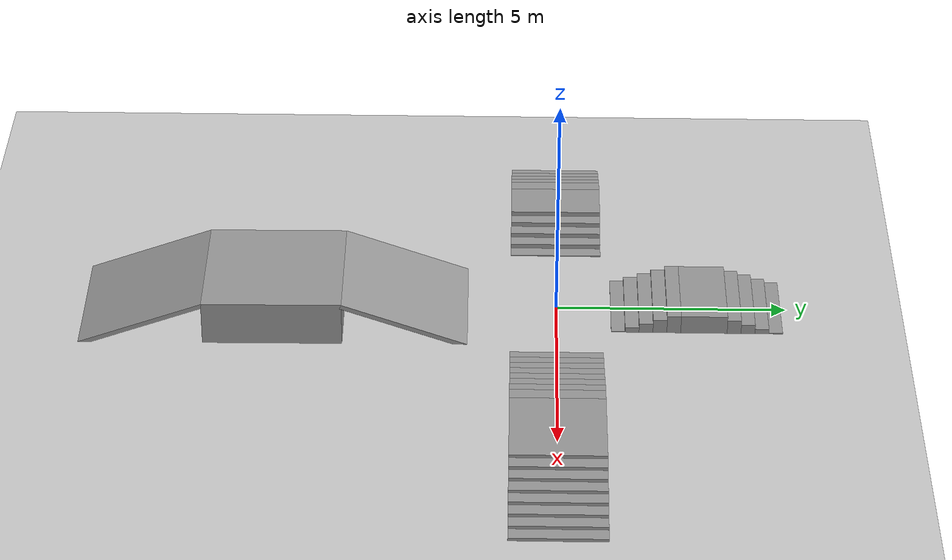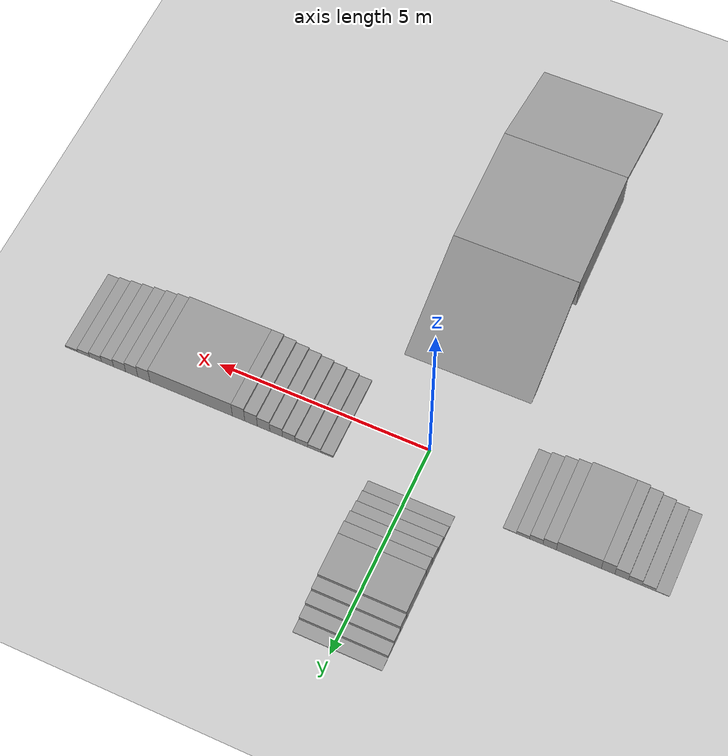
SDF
<sdf version="1.7">
 <world name="default">
  <light name="sun" type="directional">
   <pose>0 0 10 0 -0 0</pose>
   <diffuse>0.8 0.8 0.8 1</diffuse>
   <specular>0.2 0.2 0.2 1</specular>
   <attenuation>
    <range>1000</range>
    <constant>0.9</constant>
    <linear>0.01</linear>
    <quadratic>0.001</quadratic>
   </attenuation>
   <direction>-0.5 0.1 -0.9</direction>
   <spot><inner_angle>0</inner_angle><outer_angle>0</outer_angle><falloff>0</falloff></spot>
  </light>
  <model name="ground_plane">
   <static>1</static>
   <link name="link">
    <collision name="collision">
     <geometry><plane><normal>0 0 1</normal><size>100 100</size></plane></geometry>
     <surface><friction><ode><mu>100</mu><mu2>50</mu2></ode></friction></surface>
    </collision>
    <visual name="visual">
     <cast_shadows>0</cast_shadows>
     <geometry><plane><normal>0 0 1</normal><size>100 100</size></plane></geometry>
     <material>
      <script><uri>file://media/materials/scripts/gazebo.material</uri><name>Gazebo/Grey</name></script>
     </material>
    </visual>
   </link>
  </model>
  <gravity>0 0 -9.8</gravity>
  <magnetic_field>6e-06 2.3e-05 -4.2e-05</magnetic_field>
  <atmosphere type="adiabatic"/>
  <physics type="ode">
   <max_step_size>0.001</max_step_size>
   <real_time_factor>1</real_time_factor>
   <real_time_update_rate>1000</real_time_update_rate>
  </physics>
  <scene><ambient>0.4 0.4 0.4 1</ambient><background>0.7 0.7 0.7 1</background><shadows>1</shadows></scene>
  <spherical_coordinates>
   <surface_model>EARTH_WGS84</surface_model>
   <latitude_deg>0</latitude_deg>
   <longitude_deg>0</longitude_deg>
   <elevation>0</elevation>
   <heading_deg>0</heading_deg>
  </spherical_coordinates>
  <model name="7cm">
   <link name="link_0">
    <inertial>
     <mass>1</mass>
     <inertia>
      <ixx>0.166667</ixx>
      <ixy>0</ixy>
      <ixz>0</ixz>
      <iyy>0.166667</iyy>
      <iyz>0</iyz>
      <izz>0.166667</izz>
     </inertia>
    </inertial>
    <pose>-3.04688 0 -0.1225 0 -0 0</pose>
    <kinematic>1</kinematic>
    <visual name="visual">
     <geometry><box><size>0.3 2 0.07</size></box></geometry>
     <material>
      <lighting>1</lighting>
      <script><uri>file://media/materials/scripts/gazebo.material</uri><name>Gazebo/Grey</name></script>
      <shader type="pixel"><normal_map>__default__</normal_map></shader>
      <ambient>0.3 0.3 0.3 1</ambient>
      <diffuse>0.7 0.7 0.7 1</diffuse>
      <specular>0.01 0.01 0.01 1</specular>
      <emissive>0 0 0 1</emissive>
     </material>
    </visual>
    <collision name="collision">
     <geometry><box><size>0.3 2 0.07</size></box></geometry>
     <surface>
      <friction>
       <ode><mu>1</mu><mu2>1</mu2><fdir1>0 0 0</fdir1><slip1>0</slip1><slip2>0</slip2></ode>
       <torsional>
        <coefficient>1</coefficient>
        <patch_radius>0</patch_radius>
        <surface_radius>0</surface_radius>
        <use_patch_radius>1</use_patch_radius>
        <ode><slip>0</slip></ode>
       </torsional>
      </friction>
      <bounce><restitution_coefficient>0</restitution_coefficient><threshold>1e+06</threshold></bounce>
      <contact>
       <collide_without_contact>0</collide_without_contact>
       <collide_without_contact_bitmask>1</collide_without_contact_bitmask>
       <collide_bitmask>1</collide_bitmask>
       <ode>
        <soft_cfm>0</soft_cfm>
        <soft_erp>0.2</soft_erp>
        <kp>1e+13</kp>
        <kd>1</kd>
        <max_vel>0.01</max_vel>
        <min_depth>0</min_depth>
       </ode>
       <bullet>
        <split_impulse>1</split_impulse>
        <split_impulse_penetration_threshold>-0.01</split_impulse_penetration_threshold>
        <soft_cfm>0</soft_cfm>
        <soft_erp>0.2</soft_erp>
        <kp>1e+13</kp>
        <kd>1</kd>
       </bullet>
      </contact>
     </surface>
    </collision>
   </link>
   <link name="link_0_clone">
    <inertial>
     <mass>1</mass>
     <inertia>
      <ixx>0.166667</ixx>
      <ixy>0</ixy>
      <ixz>0</ixz>
      <iyy>0.166667</iyy>
      <iyz>0</iyz>
      <izz>0.166667</izz>
     </inertia>
    </inertial>
    <pose>-2.74688 0 -0.0875 0 -0 0</pose>
    <kinematic>1</kinematic>
    <visual name="visual">
     <geometry><box><size>0.3 2 0.14</size></box></geometry>
     <material>
      <lighting>1</lighting>
      <script><uri>file://media/materials/scripts/gazebo.material</uri><name>Gazebo/Grey</name></script>
      <shader type="pixel"><normal_map>__default__</normal_map></shader>
      <ambient>0.3 0.3 0.3 1</ambient>
      <diffuse>0.7 0.7 0.7 1</diffuse>
      <specular>0.01 0.01 0.01 1</specular>
      <emissive>0 0 0 1</emissive>
     </material>
    </visual>
    <collision name="collision">
     <geometry><box><size>0.3 2 0.14</size></box></geometry>
     <surface>
      <friction>
       <ode><mu>1</mu><mu2>1</mu2><fdir1>0 0 0</fdir1><slip1>0</slip1><slip2>0</slip2></ode>
       <torsional>
        <coefficient>1</coefficient>
        <patch_radius>0</patch_radius>
        <surface_radius>0</surface_radius>
        <use_patch_radius>1</use_patch_radius>
        <ode><slip>0</slip></ode>
       </torsional>
      </friction>
      <bounce><restitution_coefficient>0</restitution_coefficient><threshold>1e+06</threshold></bounce>
      <contact>
       <collide_without_contact>0</collide_without_contact>
       <collide_without_contact_bitmask>1</collide_without_contact_bitmask>
       <collide_bitmask>1</collide_bitmask>
       <ode>
        <soft_cfm>0</soft_cfm>
        <soft_erp>0.2</soft_erp>
        <kp>1e+13</kp>
        <kd>1</kd>
        <max_vel>0.01</max_vel>
        <min_depth>0</min_depth>
       </ode>
       <bullet>
        <split_impulse>1</split_impulse>
        <split_impulse_penetration_threshold>-0.01</split_impulse_penetration_threshold>
        <soft_cfm>0</soft_cfm>
        <soft_erp>0.2</soft_erp>
        <kp>1e+13</kp>
        <kd>1</kd>
       </bullet>
      </contact>
     </surface>
    </collision>
   </link>
   <link name="link_0_clone_0">
    <inertial>
     <mass>1</mass>
     <inertia>
      <ixx>0.166667</ixx>
      <ixy>0</ixy>
      <ixz>0</ixz>
      <iyy>0.166667</iyy>
      <iyz>0</iyz>
      <izz>0.166667</izz>
     </inertia>
    </inertial>
    <pose>3.15313 0 -0.1225 0 -0 0</pose>
    <kinematic>1</kinematic>
    <visual name="visual">
     <geometry><box><size>0.3 2 0.07</size></box></geometry>
     <material>
      <lighting>1</lighting>
      <script><uri>file://media/materials/scripts/gazebo.material</uri><name>Gazebo/Grey</name></script>
      <shader type="pixel"><normal_map>__default__</normal_map></shader>
      <ambient>0.3 0.3 0.3 1</ambient>
      <diffuse>0.7 0.7 0.7 1</diffuse>
      <specular>0.01 0.01 0.01 1</specular>
      <emissive>0 0 0 1</emissive>
     </material>
    </visual>
    <collision name="collision">
     <geometry><box><size>0.3 2 0.07</size></box></geometry>
     <surface>
      <friction>
       <ode><mu>1</mu><mu2>1</mu2><fdir1>0 0 0</fdir1><slip1>0</slip1><slip2>0</slip2></ode>
       <torsional>
        <coefficient>1</coefficient>
        <patch_radius>0</patch_radius>
        <surface_radius>0</surface_radius>
        <use_patch_radius>1</use_patch_radius>
        <ode><slip>0</slip></ode>
       </torsional>
      </friction>
      <bounce><restitution_coefficient>0</restitution_coefficient><threshold>1e+06</threshold></bounce>
      <contact>
       <collide_without_contact>0</collide_without_contact>
       <collide_without_contact_bitmask>1</collide_without_contact_bitmask>
       <collide_bitmask>1</collide_bitmask>
       <ode>
        <soft_cfm>0</soft_cfm>
        <soft_erp>0.2</soft_erp>
        <kp>1e+13</kp>
        <kd>1</kd>
        <max_vel>0.01</max_vel>
        <min_depth>0</min_depth>
       </ode>
       <bullet>
        <split_impulse>1</split_impulse>
        <split_impulse_penetration_threshold>-0.01</split_impulse_penetration_threshold>
        <soft_cfm>0</soft_cfm>
        <soft_erp>0.2</soft_erp>
        <kp>1e+13</kp>
        <kd>1</kd>
       </bullet>
      </contact>
     </surface>
    </collision>
   </link>
   <link name="link_0_clone_clone">
    <inertial>
     <mass>1</mass>
     <inertia>
      <ixx>0.166667</ixx>
      <ixy>0</ixy>
      <ixz>0</ixz>
      <iyy>0.166667</iyy>
      <iyz>0</iyz>
      <izz>0.166667</izz>
     </inertia>
    </inertial>
    <pose>-2.44687 0 -0.0525 0 -0 0</pose>
    <kinematic>1</kinematic>
    <visual name="visual">
     <geometry><box><size>0.3 2 0.21</size></box></geometry>
     <material>
      <lighting>1</lighting>
      <script><uri>file://media/materials/scripts/gazebo.material</uri><name>Gazebo/Grey</name></script>
      <shader type="pixel"><normal_map>__default__</normal_map></shader>
      <ambient>0.3 0.3 0.3 1</ambient>
      <diffuse>0.7 0.7 0.7 1</diffuse>
      <specular>0.01 0.01 0.01 1</specular>
      <emissive>0 0 0 1</emissive>
     </material>
    </visual>
    <collision name="collision">
     <geometry><box><size>0.3 2 0.21</size></box></geometry>
     <surface>
      <friction>
       <ode><mu>1</mu><mu2>1</mu2><fdir1>0 0 0</fdir1><slip1>0</slip1><slip2>0</slip2></ode>
       <torsional>
        <coefficient>1</coefficient>
        <patch_radius>0</patch_radius>
        <surface_radius>0</surface_radius>
        <use_patch_radius>1</use_patch_radius>
        <ode><slip>0</slip></ode>
       </torsional>
      </friction>
      <bounce><restitution_coefficient>0</restitution_coefficient><threshold>1e+06</threshold></bounce>
      <contact>
       <collide_without_contact>0</collide_without_contact>
       <collide_without_contact_bitmask>1</collide_without_contact_bitmask>
       <collide_bitmask>1</collide_bitmask>
       <ode>
        <soft_cfm>0</soft_cfm>
        <soft_erp>0.2</soft_erp>
        <kp>1e+13</kp>
        <kd>1</kd>
        <max_vel>0.01</max_vel>
        <min_depth>0</min_depth>
       </ode>
       <bullet>
        <split_impulse>1</split_impulse>
        <split_impulse_penetration_threshold>-0.01</split_impulse_penetration_threshold>
        <soft_cfm>0</soft_cfm>
        <soft_erp>0.2</soft_erp>
        <kp>1e+13</kp>
        <kd>1</kd>
       </bullet>
      </contact>
     </surface>
    </collision>
   </link>
   <link name="link_0_clone_clone_0">
    <inertial>
     <mass>1</mass>
     <inertia>
      <ixx>0.166667</ixx>
      <ixy>0</ixy>
      <ixz>0</ixz>
      <iyy>0.166667</iyy>
      <iyz>0</iyz>
      <izz>0.166667</izz>
     </inertia>
    </inertial>
    <pose>2.85312 0 -0.0875 0 -0 0</pose>
    <kinematic>1</kinematic>
    <visual name="visual">
     <geometry><box><size>0.3 2 0.14</size></box></geometry>
     <material>
      <lighting>1</lighting>
      <script><uri>file://media/materials/scripts/gazebo.material</uri><name>Gazebo/Grey</name></script>
      <shader type="pixel"><normal_map>__default__</normal_map></shader>
      <ambient>0.3 0.3 0.3 1</ambient>
      <diffuse>0.7 0.7 0.7 1</diffuse>
      <specular>0.01 0.01 0.01 1</specular>
      <emissive>0 0 0 1</emissive>
     </material>
    </visual>
    <collision name="collision">
     <geometry><box><size>0.3 2 0.14</size></box></geometry>
     <surface>
      <friction>
       <ode><mu>1</mu><mu2>1</mu2><fdir1>0 0 0</fdir1><slip1>0</slip1><slip2>0</slip2></ode>
       <torsional>
        <coefficient>1</coefficient>
        <patch_radius>0</patch_radius>
        <surface_radius>0</surface_radius>
        <use_patch_radius>1</use_patch_radius>
        <ode><slip>0</slip></ode>
       </torsional>
      </friction>
      <bounce><restitution_coefficient>0</restitution_coefficient><threshold>1e+06</threshold></bounce>
      <contact>
       <collide_without_contact>0</collide_without_contact>
       <collide_without_contact_bitmask>1</collide_without_contact_bitmask>
       <collide_bitmask>1</collide_bitmask>
       <ode>
        <soft_cfm>0</soft_cfm>
        <soft_erp>0.2</soft_erp>
        <kp>1e+13</kp>
        <kd>1</kd>
        <max_vel>0.01</max_vel>
        <min_depth>0</min_depth>
       </ode>
       <bullet>
        <split_impulse>1</split_impulse>
        <split_impulse_penetration_threshold>-0.01</split_impulse_penetration_threshold>
        <soft_cfm>0</soft_cfm>
        <soft_erp>0.2</soft_erp>
        <kp>1e+13</kp>
        <kd>1</kd>
       </bullet>
      </contact>
     </surface>
    </collision>
   </link>
   <link name="link_0_clone_clone_clone">
    <inertial>
     <mass>1</mass>
     <inertia>
      <ixx>0.166667</ixx>
      <ixy>0</ixy>
      <ixz>0</ixz>
      <iyy>0.166667</iyy>
      <iyz>0</iyz>
      <izz>0.166667</izz>
     </inertia>
    </inertial>
    <pose>-2.14688 0 -0.0175 0 -0 0</pose>
    <kinematic>1</kinematic>
    <visual name="visual">
     <geometry><box><size>0.3 2 0.28</size></box></geometry>
     <material>
      <lighting>1</lighting>
      <script><uri>file://media/materials/scripts/gazebo.material</uri><name>Gazebo/Grey</name></script>
      <shader type="pixel"><normal_map>__default__</normal_map></shader>
      <ambient>0.3 0.3 0.3 1</ambient>
      <diffuse>0.7 0.7 0.7 1</diffuse>
      <specular>0.01 0.01 0.01 1</specular>
      <emissive>0 0 0 1</emissive>
     </material>
    </visual>
    <collision name="collision">
     <geometry><box><size>0.3 2 0.28</size></box></geometry>
     <surface>
      <friction>
       <ode><mu>1</mu><mu2>1</mu2><fdir1>0 0 0</fdir1><slip1>0</slip1><slip2>0</slip2></ode>
       <torsional>
        <coefficient>1</coefficient>
        <patch_radius>0</patch_radius>
        <surface_radius>0</surface_radius>
        <use_patch_radius>1</use_patch_radius>
        <ode><slip>0</slip></ode>
       </torsional>
      </friction>
      <bounce><restitution_coefficient>0</restitution_coefficient><threshold>1e+06</threshold></bounce>
      <contact>
       <collide_without_contact>0</collide_without_contact>
       <collide_without_contact_bitmask>1</collide_without_contact_bitmask>
       <collide_bitmask>1</collide_bitmask>
       <ode>
        <soft_cfm>0</soft_cfm>
        <soft_erp>0.2</soft_erp>
        <kp>1e+13</kp>
        <kd>1</kd>
        <max_vel>0.01</max_vel>
        <min_depth>0</min_depth>
       </ode>
       <bullet>
        <split_impulse>1</split_impulse>
        <split_impulse_penetration_threshold>-0.01</split_impulse_penetration_threshold>
        <soft_cfm>0</soft_cfm>
        <soft_erp>0.2</soft_erp>
        <kp>1e+13</kp>
        <kd>1</kd>
       </bullet>
      </contact>
     </surface>
    </collision>
   </link>
   <link name="link_0_clone_clone_clone_0">
    <inertial>
     <mass>1</mass>
     <inertia>
      <ixx>0.166667</ixx>
      <ixy>0</ixy>
      <ixz>0</ixz>
      <iyy>0.166667</iyy>
      <iyz>0</iyz>
      <izz>0.166667</izz>
     </inertia>
    </inertial>
    <pose>2.55313 0 -0.0525 0 -0 0</pose>
    <kinematic>1</kinematic>
    <visual name="visual">
     <geometry><box><size>0.3 2 0.21</size></box></geometry>
     <material>
      <lighting>1</lighting>
      <script><uri>file://media/materials/scripts/gazebo.material</uri><name>Gazebo/Grey</name></script>
      <shader type="pixel"><normal_map>__default__</normal_map></shader>
      <ambient>0.3 0.3 0.3 1</ambient>
      <diffuse>0.7 0.7 0.7 1</diffuse>
      <specular>0.01 0.01 0.01 1</specular>
      <emissive>0 0 0 1</emissive>
     </material>
    </visual>
    <collision name="collision">
     <geometry><box><size>0.3 2 0.21</size></box></geometry>
     <surface>
      <friction>
       <ode><mu>1</mu><mu2>1</mu2><fdir1>0 0 0</fdir1><slip1>0</slip1><slip2>0</slip2></ode>
       <torsional>
        <coefficient>1</coefficient>
        <patch_radius>0</patch_radius>
        <surface_radius>0</surface_radius>
        <use_patch_radius>1</use_patch_radius>
        <ode><slip>0</slip></ode>
       </torsional>
      </friction>
      <bounce><restitution_coefficient>0</restitution_coefficient><threshold>1e+06</threshold></bounce>
      <contact>
       <collide_without_contact>0</collide_without_contact>
       <collide_without_contact_bitmask>1</collide_without_contact_bitmask>
       <collide_bitmask>1</collide_bitmask>
       <ode>
        <soft_cfm>0</soft_cfm>
        <soft_erp>0.2</soft_erp>
        <kp>1e+13</kp>
        <kd>1</kd>
        <max_vel>0.01</max_vel>
        <min_depth>0</min_depth>
       </ode>
       <bullet>
        <split_impulse>1</split_impulse>
        <split_impulse_penetration_threshold>-0.01</split_impulse_penetration_threshold>
        <soft_cfm>0</soft_cfm>
        <soft_erp>0.2</soft_erp>
        <kp>1e+13</kp>
        <kd>1</kd>
       </bullet>
      </contact>
     </surface>
    </collision>
   </link>
   <link name="link_0_clone_clone_clone_clone">
    <inertial>
     <mass>1</mass>
     <inertia>
      <ixx>0.166667</ixx>
      <ixy>0</ixy>
      <ixz>0</ixz>
      <iyy>0.166667</iyy>
      <iyz>0</iyz>
      <izz>0.166667</izz>
     </inertia>
    </inertial>
    <pose>-1.84688 0 0.0175 0 -0 0</pose>
    <kinematic>1</kinematic>
    <visual name="visual">
     <geometry><box><size>0.3 2 0.35</size></box></geometry>
     <material>
      <lighting>1</lighting>
      <script><uri>file://media/materials/scripts/gazebo.material</uri><name>Gazebo/Grey</name></script>
      <shader type="pixel"><normal_map>__default__</normal_map></shader>
      <ambient>0.3 0.3 0.3 1</ambient>
      <diffuse>0.7 0.7 0.7 1</diffuse>
      <specular>0.01 0.01 0.01 1</specular>
      <emissive>0 0 0 1</emissive>
     </material>
    </visual>
    <collision name="collision">
     <geometry><box><size>0.3 2 0.35</size></box></geometry>
     <surface>
      <friction>
       <ode><mu>1</mu><mu2>1</mu2><fdir1>0 0 0</fdir1><slip1>0</slip1><slip2>0</slip2></ode>
       <torsional>
        <coefficient>1</coefficient>
        <patch_radius>0</patch_radius>
        <surface_radius>0</surface_radius>
        <use_patch_radius>1</use_patch_radius>
        <ode><slip>0</slip></ode>
       </torsional>
      </friction>
      <bounce><restitution_coefficient>0</restitution_coefficient><threshold>1e+06</threshold></bounce>
      <contact>
       <collide_without_contact>0</collide_without_contact>
       <collide_without_contact_bitmask>1</collide_without_contact_bitmask>
       <collide_bitmask>1</collide_bitmask>
       <ode>
        <soft_cfm>0</soft_cfm>
        <soft_erp>0.2</soft_erp>
        <kp>1e+13</kp>
        <kd>1</kd>
        <max_vel>0.01</max_vel>
        <min_depth>0</min_depth>
       </ode>
       <bullet>
        <split_impulse>1</split_impulse>
        <split_impulse_penetration_threshold>-0.01</split_impulse_penetration_threshold>
        <soft_cfm>0</soft_cfm>
        <soft_erp>0.2</soft_erp>
        <kp>1e+13</kp>
        <kd>1</kd>
       </bullet>
      </contact>
     </surface>
    </collision>
   </link>
   <link name="link_0_clone_clone_clone_clone_0">
    <inertial>
     <mass>1</mass>
     <inertia>
      <ixx>0.166667</ixx>
      <ixy>0</ixy>
      <ixz>0</ixz>
      <iyy>0.166667</iyy>
      <iyz>0</iyz>
      <izz>0.166667</izz>
     </inertia>
    </inertial>
    <pose>2.25312 0 -0.0175 0 -0 0</pose>
    <kinematic>1</kinematic>
    <visual name="visual">
     <geometry><box><size>0.3 2 0.28</size></box></geometry>
     <material>
      <lighting>1</lighting>
      <script><uri>file://media/materials/scripts/gazebo.material</uri><name>Gazebo/Grey</name></script>
      <shader type="pixel"><normal_map>__default__</normal_map></shader>
      <ambient>0.3 0.3 0.3 1</ambient>
      <diffuse>0.7 0.7 0.7 1</diffuse>
      <specular>0.01 0.01 0.01 1</specular>
      <emissive>0 0 0 1</emissive>
     </material>
    </visual>
    <collision name="collision">
     <geometry><box><size>0.3 2 0.28</size></box></geometry>
     <surface>
      <friction>
       <ode><mu>1</mu><mu2>1</mu2><fdir1>0 0 0</fdir1><slip1>0</slip1><slip2>0</slip2></ode>
       <torsional>
        <coefficient>1</coefficient>
        <patch_radius>0</patch_radius>
        <surface_radius>0</surface_radius>
        <use_patch_radius>1</use_patch_radius>
        <ode><slip>0</slip></ode>
       </torsional>
      </friction>
      <bounce><restitution_coefficient>0</restitution_coefficient><threshold>1e+06</threshold></bounce>
      <contact>
       <collide_without_contact>0</collide_without_contact>
       <collide_without_contact_bitmask>1</collide_without_contact_bitmask>
       <collide_bitmask>1</collide_bitmask>
       <ode>
        <soft_cfm>0</soft_cfm>
        <soft_erp>0.2</soft_erp>
        <kp>1e+13</kp>
        <kd>1</kd>
        <max_vel>0.01</max_vel>
        <min_depth>0</min_depth>
       </ode>
       <bullet>
        <split_impulse>1</split_impulse>
        <split_impulse_penetration_threshold>-0.01</split_impulse_penetration_threshold>
        <soft_cfm>0</soft_cfm>
        <soft_erp>0.2</soft_erp>
        <kp>1e+13</kp>
        <kd>1</kd>
       </bullet>
      </contact>
     </surface>
    </collision>
   </link>
   <link name="link_0_clone_clone_clone_clone_clone">
    <inertial>
     <mass>1</mass>
     <inertia>
      <ixx>0.166667</ixx>
      <ixy>0</ixy>
      <ixz>0</ixz>
      <iyy>0.166667</iyy>
      <iyz>0</iyz>
      <izz>0.166667</izz>
     </inertia>
    </inertial>
    <pose>-1.54688 0 0.0525 0 -0 0</pose>
    <kinematic>1</kinematic>
    <visual name="visual">
     <geometry><box><size>0.3 2 0.42</size></box></geometry>
     <material>
      <lighting>1</lighting>
      <script><uri>file://media/materials/scripts/gazebo.material</uri><name>Gazebo/Grey</name></script>
      <shader type="pixel"><normal_map>__default__</normal_map></shader>
      <ambient>0.3 0.3 0.3 1</ambient>
      <diffuse>0.7 0.7 0.7 1</diffuse>
      <specular>0.01 0.01 0.01 1</specular>
      <emissive>0 0 0 1</emissive>
     </material>
    </visual>
    <collision name="collision">
     <geometry><box><size>0.3 2 0.42</size></box></geometry>
     <surface>
      <friction>
       <ode><mu>1</mu><mu2>1</mu2><fdir1>0 0 0</fdir1><slip1>0</slip1><slip2>0</slip2></ode>
       <torsional>
        <coefficient>1</coefficient>
        <patch_radius>0</patch_radius>
        <surface_radius>0</surface_radius>
        <use_patch_radius>1</use_patch_radius>
        <ode><slip>0</slip></ode>
       </torsional>
      </friction>
      <bounce><restitution_coefficient>0</restitution_coefficient><threshold>1e+06</threshold></bounce>
      <contact>
       <collide_without_contact>0</collide_without_contact>
       <collide_without_contact_bitmask>1</collide_without_contact_bitmask>
       <collide_bitmask>1</collide_bitmask>
       <ode>
        <soft_cfm>0</soft_cfm>
        <soft_erp>0.2</soft_erp>
        <kp>1e+13</kp>
        <kd>1</kd>
        <max_vel>0.01</max_vel>
        <min_depth>0</min_depth>
       </ode>
       <bullet>
        <split_impulse>1</split_impulse>
        <split_impulse_penetration_threshold>-0.01</split_impulse_penetration_threshold>
        <soft_cfm>0</soft_cfm>
        <soft_erp>0.2</soft_erp>
        <kp>1e+13</kp>
        <kd>1</kd>
       </bullet>
      </contact>
     </surface>
    </collision>
   </link>
   <link name="link_0_clone_clone_clone_clone_clone_0">
    <inertial>
     <mass>1</mass>
     <inertia>
      <ixx>0.166667</ixx>
      <ixy>0</ixy>
      <ixz>0</ixz>
      <iyy>0.166667</iyy>
      <iyz>0</iyz>
      <izz>0.166667</izz>
     </inertia>
    </inertial>
    <pose>1.95312 0 0.0175 0 -0 0</pose>
    <kinematic>1</kinematic>
    <visual name="visual">
     <geometry><box><size>0.3 2 0.35</size></box></geometry>
     <material>
      <lighting>1</lighting>
      <script><uri>file://media/materials/scripts/gazebo.material</uri><name>Gazebo/Grey</name></script>
      <shader type="pixel"><normal_map>__default__</normal_map></shader>
      <ambient>0.3 0.3 0.3 1</ambient>
      <diffuse>0.7 0.7 0.7 1</diffuse>
      <specular>0.01 0.01 0.01 1</specular>
      <emissive>0 0 0 1</emissive>
     </material>
    </visual>
    <collision name="collision">
     <geometry><box><size>0.3 2 0.35</size></box></geometry>
     <surface>
      <friction>
       <ode><mu>1</mu><mu2>1</mu2><fdir1>0 0 0</fdir1><slip1>0</slip1><slip2>0</slip2></ode>
       <torsional>
        <coefficient>1</coefficient>
        <patch_radius>0</patch_radius>
        <surface_radius>0</surface_radius>
        <use_patch_radius>1</use_patch_radius>
        <ode><slip>0</slip></ode>
       </torsional>
      </friction>
      <bounce><restitution_coefficient>0</restitution_coefficient><threshold>1e+06</threshold></bounce>
      <contact>
       <collide_without_contact>0</collide_without_contact>
       <collide_without_contact_bitmask>1</collide_without_contact_bitmask>
       <collide_bitmask>1</collide_bitmask>
       <ode>
        <soft_cfm>0</soft_cfm>
        <soft_erp>0.2</soft_erp>
        <kp>1e+13</kp>
        <kd>1</kd>
        <max_vel>0.01</max_vel>
        <min_depth>0</min_depth>
       </ode>
       <bullet>
        <split_impulse>1</split_impulse>
        <split_impulse_penetration_threshold>-0.01</split_impulse_penetration_threshold>
        <soft_cfm>0</soft_cfm>
        <soft_erp>0.2</soft_erp>
        <kp>1e+13</kp>
        <kd>1</kd>
       </bullet>
      </contact>
     </surface>
    </collision>
   </link>
   <link name="link_0_clone_clone_clone_clone_clone_clone">
    <inertial>
     <mass>1</mass>
     <inertia>
      <ixx>0.166667</ixx>
      <ixy>0</ixy>
      <ixz>0</ixz>
      <iyy>0.166667</iyy>
      <iyz>0</iyz>
      <izz>0.166667</izz>
     </inertia>
    </inertial>
    <pose>-1.24687 0 0.0875 0 -0 0</pose>
    <kinematic>1</kinematic>
    <visual name="visual">
     <geometry><box><size>0.3 2 0.49</size></box></geometry>
     <material>
      <lighting>1</lighting>
      <script><uri>file://media/materials/scripts/gazebo.material</uri><name>Gazebo/Grey</name></script>
      <shader type="pixel"><normal_map>__default__</normal_map></shader>
      <ambient>0.3 0.3 0.3 1</ambient>
      <diffuse>0.7 0.7 0.7 1</diffuse>
      <specular>0.01 0.01 0.01 1</specular>
      <emissive>0 0 0 1</emissive>
     </material>
    </visual>
    <collision name="collision">
     <geometry><box><size>0.3 2 0.49</size></box></geometry>
     <surface>
      <friction>
       <ode><mu>1</mu><mu2>1</mu2><fdir1>0 0 0</fdir1><slip1>0</slip1><slip2>0</slip2></ode>
       <torsional>
        <coefficient>1</coefficient>
        <patch_radius>0</patch_radius>
        <surface_radius>0</surface_radius>
        <use_patch_radius>1</use_patch_radius>
        <ode><slip>0</slip></ode>
       </torsional>
      </friction>
      <bounce><restitution_coefficient>0</restitution_coefficient><threshold>1e+06</threshold></bounce>
      <contact>
       <collide_without_contact>0</collide_without_contact>
       <collide_without_contact_bitmask>1</collide_without_contact_bitmask>
       <collide_bitmask>1</collide_bitmask>
       <ode>
        <soft_cfm>0</soft_cfm>
        <soft_erp>0.2</soft_erp>
        <kp>1e+13</kp>
        <kd>1</kd>
        <max_vel>0.01</max_vel>
        <min_depth>0</min_depth>
       </ode>
       <bullet>
        <split_impulse>1</split_impulse>
        <split_impulse_penetration_threshold>-0.01</split_impulse_penetration_threshold>
        <soft_cfm>0</soft_cfm>
        <soft_erp>0.2</soft_erp>
        <kp>1e+13</kp>
        <kd>1</kd>
       </bullet>
      </contact>
     </surface>
    </collision>
   </link>
   <link name="link_0_clone_clone_clone_clone_clone_clone_0">
    <inertial>
     <mass>1</mass>
     <inertia>
      <ixx>0.166667</ixx>
      <ixy>0</ixy>
      <ixz>0</ixz>
      <iyy>0.166667</iyy>
      <iyz>0</iyz>
      <izz>0.166667</izz>
     </inertia>
    </inertial>
    <pose>1.65312 0 0.0525 0 -0 0</pose>
    <kinematic>1</kinematic>
    <visual name="visual">
     <geometry><box><size>0.3 2 0.42</size></box></geometry>
     <material>
      <lighting>1</lighting>
      <script><uri>file://media/materials/scripts/gazebo.material</uri><name>Gazebo/Grey</name></script>
      <shader type="pixel"><normal_map>__default__</normal_map></shader>
      <ambient>0.3 0.3 0.3 1</ambient>
      <diffuse>0.7 0.7 0.7 1</diffuse>
      <specular>0.01 0.01 0.01 1</specular>
      <emissive>0 0 0 1</emissive>
     </material>
    </visual>
    <collision name="collision">
     <geometry><box><size>0.3 2 0.42</size></box></geometry>
     <surface>
      <friction>
       <ode><mu>1</mu><mu2>1</mu2><fdir1>0 0 0</fdir1><slip1>0</slip1><slip2>0</slip2></ode>
       <torsional>
        <coefficient>1</coefficient>
        <patch_radius>0</patch_radius>
        <surface_radius>0</surface_radius>
        <use_patch_radius>1</use_patch_radius>
        <ode><slip>0</slip></ode>
       </torsional>
      </friction>
      <bounce><restitution_coefficient>0</restitution_coefficient><threshold>1e+06</threshold></bounce>
      <contact>
       <collide_without_contact>0</collide_without_contact>
       <collide_without_contact_bitmask>1</collide_without_contact_bitmask>
       <collide_bitmask>1</collide_bitmask>
       <ode>
        <soft_cfm>0</soft_cfm>
        <soft_erp>0.2</soft_erp>
        <kp>1e+13</kp>
        <kd>1</kd>
        <max_vel>0.01</max_vel>
        <min_depth>0</min_depth>
       </ode>
       <bullet>
        <split_impulse>1</split_impulse>
        <split_impulse_penetration_threshold>-0.01</split_impulse_penetration_threshold>
        <soft_cfm>0</soft_cfm>
        <soft_erp>0.2</soft_erp>
        <kp>1e+13</kp>
        <kd>1</kd>
       </bullet>
      </contact>
     </surface>
    </collision>
   </link>
   <link name="link_0_clone_clone_clone_clone_clone_clone_clone">
    <inertial>
     <mass>1</mass>
     <inertia>
      <ixx>0.166667</ixx>
      <ixy>0</ixy>
      <ixz>0</ixz>
      <iyy>0.166667</iyy>
      <iyz>0</iyz>
      <izz>0.166667</izz>
     </inertia>
    </inertial>
    <pose>-0.946875 0 0.1225 0 -0 0</pose>
    <kinematic>1</kinematic>
    <visual name="visual">
     <geometry><box><size>0.3 2 0.56</size></box></geometry>
     <material>
      <lighting>1</lighting>
      <script><uri>file://media/materials/scripts/gazebo.material</uri><name>Gazebo/Grey</name></script>
      <shader type="pixel"><normal_map>__default__</normal_map></shader>
      <ambient>0.3 0.3 0.3 1</ambient>
      <diffuse>0.7 0.7 0.7 1</diffuse>
      <specular>0.01 0.01 0.01 1</specular>
      <emissive>0 0 0 1</emissive>
     </material>
    </visual>
    <collision name="collision">
     <geometry><box><size>0.3 2 0.56</size></box></geometry>
     <surface>
      <friction>
       <ode><mu>1</mu><mu2>1</mu2><fdir1>0 0 0</fdir1><slip1>0</slip1><slip2>0</slip2></ode>
       <torsional>
        <coefficient>1</coefficient>
        <patch_radius>0</patch_radius>
        <surface_radius>0</surface_radius>
        <use_patch_radius>1</use_patch_radius>
        <ode><slip>0</slip></ode>
       </torsional>
      </friction>
      <bounce><restitution_coefficient>0</restitution_coefficient><threshold>1e+06</threshold></bounce>
      <contact>
       <collide_without_contact>0</collide_without_contact>
       <collide_without_contact_bitmask>1</collide_without_contact_bitmask>
       <collide_bitmask>1</collide_bitmask>
       <ode>
        <soft_cfm>0</soft_cfm>
        <soft_erp>0.2</soft_erp>
        <kp>1e+13</kp>
        <kd>1</kd>
        <max_vel>0.01</max_vel>
        <min_depth>0</min_depth>
       </ode>
       <bullet>
        <split_impulse>1</split_impulse>
        <split_impulse_penetration_threshold>-0.01</split_impulse_penetration_threshold>
        <soft_cfm>0</soft_cfm>
        <soft_erp>0.2</soft_erp>
        <kp>1e+13</kp>
        <kd>1</kd>
       </bullet>
      </contact>
     </surface>
    </collision>
   </link>
   <link name="link_0_clone_clone_clone_clone_clone_clone_clone_0">
    <inertial>
     <mass>1</mass>
     <inertia>
      <ixx>0.166667</ixx>
      <ixy>0</ixy>
      <ixz>0</ixz>
      <iyy>0.166667</iyy>
      <iyz>0</iyz>
      <izz>0.166667</izz>
     </inertia>
    </inertial>
    <pose>1.35312 0 0.0875 0 -0 0</pose>
    <kinematic>1</kinematic>
    <visual name="visual">
     <geometry><box><size>0.3 2 0.49</size></box></geometry>
     <material>
      <lighting>1</lighting>
      <script><uri>file://media/materials/scripts/gazebo.material</uri><name>Gazebo/Grey</name></script>
      <shader type="pixel"><normal_map>__default__</normal_map></shader>
      <ambient>0.3 0.3 0.3 1</ambient>
      <diffuse>0.7 0.7 0.7 1</diffuse>
      <specular>0.01 0.01 0.01 1</specular>
      <emissive>0 0 0 1</emissive>
     </material>
    </visual>
    <collision name="collision">
     <geometry><box><size>0.3 2 0.49</size></box></geometry>
     <surface>
      <friction>
       <ode><mu>1</mu><mu2>1</mu2><fdir1>0 0 0</fdir1><slip1>0</slip1><slip2>0</slip2></ode>
       <torsional>
        <coefficient>1</coefficient>
        <patch_radius>0</patch_radius>
        <surface_radius>0</surface_radius>
        <use_patch_radius>1</use_patch_radius>
        <ode><slip>0</slip></ode>
       </torsional>
      </friction>
      <bounce><restitution_coefficient>0</restitution_coefficient><threshold>1e+06</threshold></bounce>
      <contact>
       <collide_without_contact>0</collide_without_contact>
       <collide_without_contact_bitmask>1</collide_without_contact_bitmask>
       <collide_bitmask>1</collide_bitmask>
       <ode>
        <soft_cfm>0</soft_cfm>
        <soft_erp>0.2</soft_erp>
        <kp>1e+13</kp>
        <kd>1</kd>
        <max_vel>0.01</max_vel>
        <min_depth>0</min_depth>
       </ode>
       <bullet>
        <split_impulse>1</split_impulse>
        <split_impulse_penetration_threshold>-0.01</split_impulse_penetration_threshold>
        <soft_cfm>0</soft_cfm>
        <soft_erp>0.2</soft_erp>
        <kp>1e+13</kp>
        <kd>1</kd>
       </bullet>
      </contact>
     </surface>
    </collision>
   </link>
   <link name="link_0_clone_clone_clone_clone_clone_clone_clone_clone">
    <inertial>
     <mass>1</mass>
     <inertia>
      <ixx>0.166667</ixx>
      <ixy>0</ixy>
      <ixz>0</ixz>
      <iyy>0.166667</iyy>
      <iyz>0</iyz>
      <izz>0.166667</izz>
     </inertia>
    </inertial>
    <pose>0.203125 0 0.1225 0 -0 0</pose>
    <kinematic>1</kinematic>
    <visual name="visual">
     <geometry><box><size>2 2 0.56</size></box></geometry>
     <material>
      <lighting>1</lighting>
      <script><uri>file://media/materials/scripts/gazebo.material</uri><name>Gazebo/Grey</name></script>
      <shader type="pixel"><normal_map>__default__</normal_map></shader>
      <ambient>0.3 0.3 0.3 1</ambient>
      <diffuse>0.7 0.7 0.7 1</diffuse>
      <specular>0.01 0.01 0.01 1</specular>
      <emissive>0 0 0 1</emissive>
     </material>
    </visual>
    <collision name="collision">
     <geometry><box><size>2 2 0.56</size></box></geometry>
     <surface>
      <friction>
       <ode><mu>1</mu><mu2>1</mu2><fdir1>0 0 0</fdir1><slip1>0</slip1><slip2>0</slip2></ode>
       <torsional>
        <coefficient>1</coefficient>
        <patch_radius>0</patch_radius>
        <surface_radius>0</surface_radius>
        <use_patch_radius>1</use_patch_radius>
        <ode><slip>0</slip></ode>
       </torsional>
      </friction>
      <bounce><restitution_coefficient>0</restitution_coefficient><threshold>1e+06</threshold></bounce>
      <contact>
       <collide_without_contact>0</collide_without_contact>
       <collide_without_contact_bitmask>1</collide_without_contact_bitmask>
       <collide_bitmask>1</collide_bitmask>
       <ode>
        <soft_cfm>0</soft_cfm>
        <soft_erp>0.2</soft_erp>
        <kp>1e+13</kp>
        <kd>1</kd>
        <max_vel>0.01</max_vel>
        <min_depth>0</min_depth>
       </ode>
       <bullet>
        <split_impulse>1</split_impulse>
        <split_impulse_penetration_threshold>-0.01</split_impulse_penetration_threshold>
        <soft_cfm>0</soft_cfm>
        <soft_erp>0.2</soft_erp>
        <kp>1e+13</kp>
        <kd>1</kd>
       </bullet>
      </contact>
     </surface>
    </collision>
   </link>
   <static>0</static>
   <pose>5 0 0.14 0 -0 0</pose>
  </model>
  <model name="10cm">
   <link name="link_0">
    <inertial>
     <mass>1</mass>
     <inertia>
      <ixx>0.166667</ixx>
      <ixy>0</ixy>
      <ixz>0</ixz>
      <iyy>0.166667</iyy>
      <iyz>0</iyz>
      <izz>0.166667</izz>
     </inertia>
    </inertial>
    <pose>-1.665 0 -0.1 0 -0 0</pose>
    <kinematic>1</kinematic>
    <visual name="visual">
     <geometry><box><size>0.3 2 0.1</size></box></geometry>
     <material>
      <lighting>1</lighting>
      <script><uri>file://media/materials/scripts/gazebo.material</uri><name>Gazebo/Grey</name></script>
      <shader type="pixel"><normal_map>__default__</normal_map></shader>
      <ambient>0.3 0.3 0.3 1</ambient>
      <diffuse>0.7 0.7 0.7 1</diffuse>
      <specular>0.01 0.01 0.01 1</specular>
      <emissive>0 0 0 1</emissive>
     </material>
    </visual>
    <collision name="collision">
     <geometry><box><size>0.3 2 0.1</size></box></geometry>
     <surface>
      <friction>
       <ode><mu>1</mu><mu2>1</mu2><fdir1>0 0 0</fdir1><slip1>0</slip1><slip2>0</slip2></ode>
       <torsional>
        <coefficient>1</coefficient>
        <patch_radius>0</patch_radius>
        <surface_radius>0</surface_radius>
        <use_patch_radius>1</use_patch_radius>
        <ode><slip>0</slip></ode>
       </torsional>
      </friction>
      <bounce><restitution_coefficient>0</restitution_coefficient><threshold>1e+06</threshold></bounce>
      <contact>
       <collide_without_contact>0</collide_without_contact>
       <collide_without_contact_bitmask>1</collide_without_contact_bitmask>
       <collide_bitmask>1</collide_bitmask>
       <ode>
        <soft_cfm>0</soft_cfm>
        <soft_erp>0.2</soft_erp>
        <kp>1e+13</kp>
        <kd>1</kd>
        <max_vel>0.01</max_vel>
        <min_depth>0</min_depth>
       </ode>
       <bullet>
        <split_impulse>1</split_impulse>
        <split_impulse_penetration_threshold>-0.01</split_impulse_penetration_threshold>
        <soft_cfm>0</soft_cfm>
        <soft_erp>0.2</soft_erp>
        <kp>1e+13</kp>
        <kd>1</kd>
       </bullet>
      </contact>
     </surface>
    </collision>
   </link>
   <link name="link_0_clone">
    <inertial>
     <mass>1</mass>
     <inertia>
      <ixx>0.166667</ixx>
      <ixy>0</ixy>
      <ixz>0</ixz>
      <iyy>0.166667</iyy>
      <iyz>0</iyz>
      <izz>0.166667</izz>
     </inertia>
    </inertial>
    <pose>-1.365 0 -0.05 0 -0 0</pose>
    <kinematic>1</kinematic>
    <visual name="visual">
     <geometry><box><size>0.3 2 0.2</size></box></geometry>
     <material>
      <lighting>1</lighting>
      <script><uri>file://media/materials/scripts/gazebo.material</uri><name>Gazebo/Grey</name></script>
      <shader type="pixel"><normal_map>__default__</normal_map></shader>
      <ambient>0.3 0.3 0.3 1</ambient>
      <diffuse>0.7 0.7 0.7 1</diffuse>
      <specular>0.01 0.01 0.01 1</specular>
      <emissive>0 0 0 1</emissive>
     </material>
    </visual>
    <collision name="collision">
     <geometry><box><size>0.3 2 0.2</size></box></geometry>
     <surface>
      <friction>
       <ode><mu>1</mu><mu2>1</mu2><fdir1>0 0 0</fdir1><slip1>0</slip1><slip2>0</slip2></ode>
       <torsional>
        <coefficient>1</coefficient>
        <patch_radius>0</patch_radius>
        <surface_radius>0</surface_radius>
        <use_patch_radius>1</use_patch_radius>
        <ode><slip>0</slip></ode>
       </torsional>
      </friction>
      <bounce><restitution_coefficient>0</restitution_coefficient><threshold>1e+06</threshold></bounce>
      <contact>
       <collide_without_contact>0</collide_without_contact>
       <collide_without_contact_bitmask>1</collide_without_contact_bitmask>
       <collide_bitmask>1</collide_bitmask>
       <ode>
        <soft_cfm>0</soft_cfm>
        <soft_erp>0.2</soft_erp>
        <kp>1e+13</kp>
        <kd>1</kd>
        <max_vel>0.01</max_vel>
        <min_depth>0</min_depth>
       </ode>
       <bullet>
        <split_impulse>1</split_impulse>
        <split_impulse_penetration_threshold>-0.01</split_impulse_penetration_threshold>
        <soft_cfm>0</soft_cfm>
        <soft_erp>0.2</soft_erp>
        <kp>1e+13</kp>
        <kd>1</kd>
       </bullet>
      </contact>
     </surface>
    </collision>
   </link>
   <link name="link_0_clone_0">
    <inertial>
     <mass>1</mass>
     <inertia>
      <ixx>0.166667</ixx>
      <ixy>0</ixy>
      <ixz>0</ixz>
      <iyy>0.166667</iyy>
      <iyz>0</iyz>
      <izz>0.166667</izz>
     </inertia>
    </inertial>
    <pose>1.735 0 -0.1 0 -0 0</pose>
    <kinematic>1</kinematic>
    <visual name="visual">
     <geometry><box><size>0.3 2 0.1</size></box></geometry>
     <material>
      <lighting>1</lighting>
      <script><uri>file://media/materials/scripts/gazebo.material</uri><name>Gazebo/Grey</name></script>
      <shader type="pixel"><normal_map>__default__</normal_map></shader>
      <ambient>0.3 0.3 0.3 1</ambient>
      <diffuse>0.7 0.7 0.7 1</diffuse>
      <specular>0.01 0.01 0.01 1</specular>
      <emissive>0 0 0 1</emissive>
     </material>
    </visual>
    <collision name="collision">
     <geometry><box><size>0.3 2 0.1</size></box></geometry>
     <surface>
      <friction>
       <ode><mu>1</mu><mu2>1</mu2><fdir1>0 0 0</fdir1><slip1>0</slip1><slip2>0</slip2></ode>
       <torsional>
        <coefficient>1</coefficient>
        <patch_radius>0</patch_radius>
        <surface_radius>0</surface_radius>
        <use_patch_radius>1</use_patch_radius>
        <ode><slip>0</slip></ode>
       </torsional>
      </friction>
      <bounce><restitution_coefficient>0</restitution_coefficient><threshold>1e+06</threshold></bounce>
      <contact>
       <collide_without_contact>0</collide_without_contact>
       <collide_without_contact_bitmask>1</collide_without_contact_bitmask>
       <collide_bitmask>1</collide_bitmask>
       <ode>
        <soft_cfm>0</soft_cfm>
        <soft_erp>0.2</soft_erp>
        <kp>1e+13</kp>
        <kd>1</kd>
        <max_vel>0.01</max_vel>
        <min_depth>0</min_depth>
       </ode>
       <bullet>
        <split_impulse>1</split_impulse>
        <split_impulse_penetration_threshold>-0.01</split_impulse_penetration_threshold>
        <soft_cfm>0</soft_cfm>
        <soft_erp>0.2</soft_erp>
        <kp>1e+13</kp>
        <kd>1</kd>
       </bullet>
      </contact>
     </surface>
    </collision>
   </link>
   <link name="link_0_clone_clone">
    <inertial>
     <mass>1</mass>
     <inertia>
      <ixx>0.166667</ixx>
      <ixy>0</ixy>
      <ixz>0</ixz>
      <iyy>0.166667</iyy>
      <iyz>0</iyz>
      <izz>0.166667</izz>
     </inertia>
    </inertial>
    <pose>-1.065 0 0 0 -0 0</pose>
    <kinematic>1</kinematic>
    <visual name="visual">
     <geometry><box><size>0.3 2 0.3</size></box></geometry>
     <material>
      <lighting>1</lighting>
      <script><uri>file://media/materials/scripts/gazebo.material</uri><name>Gazebo/Grey</name></script>
      <shader type="pixel"><normal_map>__default__</normal_map></shader>
      <ambient>0.3 0.3 0.3 1</ambient>
      <diffuse>0.7 0.7 0.7 1</diffuse>
      <specular>0.01 0.01 0.01 1</specular>
      <emissive>0 0 0 1</emissive>
     </material>
    </visual>
    <collision name="collision">
     <geometry><box><size>0.3 2 0.3</size></box></geometry>
     <surface>
      <friction>
       <ode><mu>1</mu><mu2>1</mu2><fdir1>0 0 0</fdir1><slip1>0</slip1><slip2>0</slip2></ode>
       <torsional>
        <coefficient>1</coefficient>
        <patch_radius>0</patch_radius>
        <surface_radius>0</surface_radius>
        <use_patch_radius>1</use_patch_radius>
        <ode><slip>0</slip></ode>
       </torsional>
      </friction>
      <bounce><restitution_coefficient>0</restitution_coefficient><threshold>1e+06</threshold></bounce>
      <contact>
       <collide_without_contact>0</collide_without_contact>
       <collide_without_contact_bitmask>1</collide_without_contact_bitmask>
       <collide_bitmask>1</collide_bitmask>
       <ode>
        <soft_cfm>0</soft_cfm>
        <soft_erp>0.2</soft_erp>
        <kp>1e+13</kp>
        <kd>1</kd>
        <max_vel>0.01</max_vel>
        <min_depth>0</min_depth>
       </ode>
       <bullet>
        <split_impulse>1</split_impulse>
        <split_impulse_penetration_threshold>-0.01</split_impulse_penetration_threshold>
        <soft_cfm>0</soft_cfm>
        <soft_erp>0.2</soft_erp>
        <kp>1e+13</kp>
        <kd>1</kd>
       </bullet>
      </contact>
     </surface>
    </collision>
   </link>
   <link name="link_0_clone_clone_0">
    <inertial>
     <mass>1</mass>
     <inertia>
      <ixx>0.166667</ixx>
      <ixy>0</ixy>
      <ixz>0</ixz>
      <iyy>0.166667</iyy>
      <iyz>0</iyz>
      <izz>0.166667</izz>
     </inertia>
    </inertial>
    <pose>1.435 0 -0.05 0 -0 0</pose>
    <kinematic>1</kinematic>
    <visual name="visual">
     <geometry><box><size>0.3 2 0.2</size></box></geometry>
     <material>
      <lighting>1</lighting>
      <script><uri>file://media/materials/scripts/gazebo.material</uri><name>Gazebo/Grey</name></script>
      <shader type="pixel"><normal_map>__default__</normal_map></shader>
      <ambient>0.3 0.3 0.3 1</ambient>
      <diffuse>0.7 0.7 0.7 1</diffuse>
      <specular>0.01 0.01 0.01 1</specular>
      <emissive>0 0 0 1</emissive>
     </material>
    </visual>
    <collision name="collision">
     <geometry><box><size>0.3 2 0.2</size></box></geometry>
     <surface>
      <friction>
       <ode><mu>1</mu><mu2>1</mu2><fdir1>0 0 0</fdir1><slip1>0</slip1><slip2>0</slip2></ode>
       <torsional>
        <coefficient>1</coefficient>
        <patch_radius>0</patch_radius>
        <surface_radius>0</surface_radius>
        <use_patch_radius>1</use_patch_radius>
        <ode><slip>0</slip></ode>
       </torsional>
      </friction>
      <bounce><restitution_coefficient>0</restitution_coefficient><threshold>1e+06</threshold></bounce>
      <contact>
       <collide_without_contact>0</collide_without_contact>
       <collide_without_contact_bitmask>1</collide_without_contact_bitmask>
       <collide_bitmask>1</collide_bitmask>
       <ode>
        <soft_cfm>0</soft_cfm>
        <soft_erp>0.2</soft_erp>
        <kp>1e+13</kp>
        <kd>1</kd>
        <max_vel>0.01</max_vel>
        <min_depth>0</min_depth>
       </ode>
       <bullet>
        <split_impulse>1</split_impulse>
        <split_impulse_penetration_threshold>-0.01</split_impulse_penetration_threshold>
        <soft_cfm>0</soft_cfm>
        <soft_erp>0.2</soft_erp>
        <kp>1e+13</kp>
        <kd>1</kd>
       </bullet>
      </contact>
     </surface>
    </collision>
   </link>
   <link name="link_0_clone_clone_clone">
    <inertial>
     <mass>1</mass>
     <inertia>
      <ixx>0.166667</ixx>
      <ixy>0</ixy>
      <ixz>0</ixz>
      <iyy>0.166667</iyy>
      <iyz>0</iyz>
      <izz>0.166667</izz>
     </inertia>
    </inertial>
    <pose>-0.765 0 0.05 0 -0 0</pose>
    <kinematic>1</kinematic>
    <visual name="visual">
     <geometry><box><size>0.3 2 0.4</size></box></geometry>
     <material>
      <lighting>1</lighting>
      <script><uri>file://media/materials/scripts/gazebo.material</uri><name>Gazebo/Grey</name></script>
      <shader type="pixel"><normal_map>__default__</normal_map></shader>
      <ambient>0.3 0.3 0.3 1</ambient>
      <diffuse>0.7 0.7 0.7 1</diffuse>
      <specular>0.01 0.01 0.01 1</specular>
      <emissive>0 0 0 1</emissive>
     </material>
    </visual>
    <collision name="collision">
     <geometry><box><size>0.3 2 0.4</size></box></geometry>
     <surface>
      <friction>
       <ode><mu>1</mu><mu2>1</mu2><fdir1>0 0 0</fdir1><slip1>0</slip1><slip2>0</slip2></ode>
       <torsional>
        <coefficient>1</coefficient>
        <patch_radius>0</patch_radius>
        <surface_radius>0</surface_radius>
        <use_patch_radius>1</use_patch_radius>
        <ode><slip>0</slip></ode>
       </torsional>
      </friction>
      <bounce><restitution_coefficient>0</restitution_coefficient><threshold>1e+06</threshold></bounce>
      <contact>
       <collide_without_contact>0</collide_without_contact>
       <collide_without_contact_bitmask>1</collide_without_contact_bitmask>
       <collide_bitmask>1</collide_bitmask>
       <ode>
        <soft_cfm>0</soft_cfm>
        <soft_erp>0.2</soft_erp>
        <kp>1e+13</kp>
        <kd>1</kd>
        <max_vel>0.01</max_vel>
        <min_depth>0</min_depth>
       </ode>
       <bullet>
        <split_impulse>1</split_impulse>
        <split_impulse_penetration_threshold>-0.01</split_impulse_penetration_threshold>
        <soft_cfm>0</soft_cfm>
        <soft_erp>0.2</soft_erp>
        <kp>1e+13</kp>
        <kd>1</kd>
       </bullet>
      </contact>
     </surface>
    </collision>
   </link>
   <link name="link_0_clone_clone_clone_0">
    <inertial>
     <mass>1</mass>
     <inertia>
      <ixx>0.166667</ixx>
      <ixy>0</ixy>
      <ixz>0</ixz>
      <iyy>0.166667</iyy>
      <iyz>0</iyz>
      <izz>0.166667</izz>
     </inertia>
    </inertial>
    <pose>1.135 0 0 0 -0 0</pose>
    <kinematic>1</kinematic>
    <visual name="visual">
     <geometry><box><size>0.3 2 0.3</size></box></geometry>
     <material>
      <lighting>1</lighting>
      <script><uri>file://media/materials/scripts/gazebo.material</uri><name>Gazebo/Grey</name></script>
      <shader type="pixel"><normal_map>__default__</normal_map></shader>
      <ambient>0.3 0.3 0.3 1</ambient>
      <diffuse>0.7 0.7 0.7 1</diffuse>
      <specular>0.01 0.01 0.01 1</specular>
      <emissive>0 0 0 1</emissive>
     </material>
    </visual>
    <collision name="collision">
     <geometry><box><size>0.3 2 0.3</size></box></geometry>
     <surface>
      <friction>
       <ode><mu>1</mu><mu2>1</mu2><fdir1>0 0 0</fdir1><slip1>0</slip1><slip2>0</slip2></ode>
       <torsional>
        <coefficient>1</coefficient>
        <patch_radius>0</patch_radius>
        <surface_radius>0</surface_radius>
        <use_patch_radius>1</use_patch_radius>
        <ode><slip>0</slip></ode>
       </torsional>
      </friction>
      <bounce><restitution_coefficient>0</restitution_coefficient><threshold>1e+06</threshold></bounce>
      <contact>
       <collide_without_contact>0</collide_without_contact>
       <collide_without_contact_bitmask>1</collide_without_contact_bitmask>
       <collide_bitmask>1</collide_bitmask>
       <ode>
        <soft_cfm>0</soft_cfm>
        <soft_erp>0.2</soft_erp>
        <kp>1e+13</kp>
        <kd>1</kd>
        <max_vel>0.01</max_vel>
        <min_depth>0</min_depth>
       </ode>
       <bullet>
        <split_impulse>1</split_impulse>
        <split_impulse_penetration_threshold>-0.01</split_impulse_penetration_threshold>
        <soft_cfm>0</soft_cfm>
        <soft_erp>0.2</soft_erp>
        <kp>1e+13</kp>
        <kd>1</kd>
       </bullet>
      </contact>
     </surface>
    </collision>
   </link>
   <link name="link_0_clone_clone_clone_clone">
    <inertial>
     <mass>1</mass>
     <inertia>
      <ixx>0.166667</ixx>
      <ixy>0</ixy>
      <ixz>0</ixz>
      <iyy>0.166667</iyy>
      <iyz>0</iyz>
      <izz>0.166667</izz>
     </inertia>
    </inertial>
    <pose>-0.465 0 0.1 0 -0 0</pose>
    <kinematic>1</kinematic>
    <visual name="visual">
     <geometry><box><size>0.3 2 0.5</size></box></geometry>
     <material>
      <lighting>1</lighting>
      <script><uri>file://media/materials/scripts/gazebo.material</uri><name>Gazebo/Grey</name></script>
      <shader type="pixel"><normal_map>__default__</normal_map></shader>
      <ambient>0.3 0.3 0.3 1</ambient>
      <diffuse>0.7 0.7 0.7 1</diffuse>
      <specular>0.01 0.01 0.01 1</specular>
      <emissive>0 0 0 1</emissive>
     </material>
    </visual>
    <collision name="collision">
     <geometry><box><size>0.3 2 0.5</size></box></geometry>
     <surface>
      <friction>
       <ode><mu>1</mu><mu2>1</mu2><fdir1>0 0 0</fdir1><slip1>0</slip1><slip2>0</slip2></ode>
       <torsional>
        <coefficient>1</coefficient>
        <patch_radius>0</patch_radius>
        <surface_radius>0</surface_radius>
        <use_patch_radius>1</use_patch_radius>
        <ode><slip>0</slip></ode>
       </torsional>
      </friction>
      <bounce><restitution_coefficient>0</restitution_coefficient><threshold>1e+06</threshold></bounce>
      <contact>
       <collide_without_contact>0</collide_without_contact>
       <collide_without_contact_bitmask>1</collide_without_contact_bitmask>
       <collide_bitmask>1</collide_bitmask>
       <ode>
        <soft_cfm>0</soft_cfm>
        <soft_erp>0.2</soft_erp>
        <kp>1e+13</kp>
        <kd>1</kd>
        <max_vel>0.01</max_vel>
        <min_depth>0</min_depth>
       </ode>
       <bullet>
        <split_impulse>1</split_impulse>
        <split_impulse_penetration_threshold>-0.01</split_impulse_penetration_threshold>
        <soft_cfm>0</soft_cfm>
        <soft_erp>0.2</soft_erp>
        <kp>1e+13</kp>
        <kd>1</kd>
       </bullet>
      </contact>
     </surface>
    </collision>
   </link>
   <link name="link_0_clone_clone_clone_clone_0">
    <inertial>
     <mass>1</mass>
     <inertia>
      <ixx>0.166667</ixx>
      <ixy>0</ixy>
      <ixz>0</ixz>
      <iyy>0.166667</iyy>
      <iyz>0</iyz>
      <izz>0.166667</izz>
     </inertia>
    </inertial>
    <pose>0.835 0 0.05 0 -0 0</pose>
    <kinematic>1</kinematic>
    <visual name="visual">
     <geometry><box><size>0.3 2 0.4</size></box></geometry>
     <material>
      <lighting>1</lighting>
      <script><uri>file://media/materials/scripts/gazebo.material</uri><name>Gazebo/Grey</name></script>
      <shader type="pixel"><normal_map>__default__</normal_map></shader>
      <ambient>0.3 0.3 0.3 1</ambient>
      <diffuse>0.7 0.7 0.7 1</diffuse>
      <specular>0.01 0.01 0.01 1</specular>
      <emissive>0 0 0 1</emissive>
     </material>
    </visual>
    <collision name="collision">
     <geometry><box><size>0.3 2 0.4</size></box></geometry>
     <surface>
      <friction>
       <ode><mu>1</mu><mu2>1</mu2><fdir1>0 0 0</fdir1><slip1>0</slip1><slip2>0</slip2></ode>
       <torsional>
        <coefficient>1</coefficient>
        <patch_radius>0</patch_radius>
        <surface_radius>0</surface_radius>
        <use_patch_radius>1</use_patch_radius>
        <ode><slip>0</slip></ode>
       </torsional>
      </friction>
      <bounce><restitution_coefficient>0</restitution_coefficient><threshold>1e+06</threshold></bounce>
      <contact>
       <collide_without_contact>0</collide_without_contact>
       <collide_without_contact_bitmask>1</collide_without_contact_bitmask>
       <collide_bitmask>1</collide_bitmask>
       <ode>
        <soft_cfm>0</soft_cfm>
        <soft_erp>0.2</soft_erp>
        <kp>1e+13</kp>
        <kd>1</kd>
        <max_vel>0.01</max_vel>
        <min_depth>0</min_depth>
       </ode>
       <bullet>
        <split_impulse>1</split_impulse>
        <split_impulse_penetration_threshold>-0.01</split_impulse_penetration_threshold>
        <soft_cfm>0</soft_cfm>
        <soft_erp>0.2</soft_erp>
        <kp>1e+13</kp>
        <kd>1</kd>
       </bullet>
      </contact>
     </surface>
    </collision>
   </link>
   <link name="link_0_clone_clone_clone_clone_clone">
    <inertial>
     <mass>1</mass>
     <inertia>
      <ixx>0.166667</ixx>
      <ixy>0</ixy>
      <ixz>0</ixz>
      <iyy>0.166667</iyy>
      <iyz>0</iyz>
      <izz>0.166667</izz>
     </inertia>
    </inertial>
    <pose>0.185 0 0.1 0 -0 0</pose>
    <kinematic>1</kinematic>
    <visual name="visual">
     <geometry><box><size>1 2 0.5</size></box></geometry>
     <material>
      <lighting>1</lighting>
      <script><uri>file://media/materials/scripts/gazebo.material</uri><name>Gazebo/Grey</name></script>
      <shader type="pixel"><normal_map>__default__</normal_map></shader>
      <ambient>0.3 0.3 0.3 1</ambient>
      <diffuse>0.7 0.7 0.7 1</diffuse>
      <specular>0.01 0.01 0.01 1</specular>
      <emissive>0 0 0 1</emissive>
     </material>
    </visual>
    <collision name="collision">
     <geometry><box><size>1 2 0.5</size></box></geometry>
     <surface>
      <friction>
       <ode><mu>1</mu><mu2>1</mu2><fdir1>0 0 0</fdir1><slip1>0</slip1><slip2>0</slip2></ode>
       <torsional>
        <coefficient>1</coefficient>
        <patch_radius>0</patch_radius>
        <surface_radius>0</surface_radius>
        <use_patch_radius>1</use_patch_radius>
        <ode><slip>0</slip></ode>
       </torsional>
      </friction>
      <bounce><restitution_coefficient>0</restitution_coefficient><threshold>1e+06</threshold></bounce>
      <contact>
       <collide_without_contact>0</collide_without_contact>
       <collide_without_contact_bitmask>1</collide_without_contact_bitmask>
       <collide_bitmask>1</collide_bitmask>
       <ode>
        <soft_cfm>0</soft_cfm>
        <soft_erp>0.2</soft_erp>
        <kp>1e+13</kp>
        <kd>1</kd>
        <max_vel>0.01</max_vel>
        <min_depth>0</min_depth>
       </ode>
       <bullet>
        <split_impulse>1</split_impulse>
        <split_impulse_penetration_threshold>-0.01</split_impulse_penetration_threshold>
        <soft_cfm>0</soft_cfm>
        <soft_erp>0.2</soft_erp>
        <kp>1e+13</kp>
        <kd>1</kd>
       </bullet>
      </contact>
     </surface>
    </collision>
   </link>
   <static>0</static>
   <pose>-0.1 3 0.05 0 -0 1.57</pose>
  </model>
  <model name="10cm_0">
   <link name="link_0">
    <inertial>
     <mass>1</mass>
     <inertia>
      <ixx>0.166667</ixx>
      <ixy>0</ixy>
      <ixz>0</ixz>
      <iyy>0.166667</iyy>
      <iyz>0</iyz>
      <izz>0.166667</izz>
     </inertia>
    </inertial>
    <pose>-1.665 0 -0.1 0 -0 0</pose>
    <kinematic>1</kinematic>
    <visual name="visual">
     <geometry><box><size>0.3 2 0.1</size></box></geometry>
     <material>
      <lighting>1</lighting>
      <script><uri>file://media/materials/scripts/gazebo.material</uri><name>Gazebo/Grey</name></script>
      <shader type="pixel"><normal_map>__default__</normal_map></shader>
      <ambient>0.3 0.3 0.3 1</ambient>
      <diffuse>0.7 0.7 0.7 1</diffuse>
      <specular>0.01 0.01 0.01 1</specular>
      <emissive>0 0 0 1</emissive>
     </material>
    </visual>
    <collision name="collision">
     <geometry><box><size>0.3 2 0.1</size></box></geometry>
     <surface>
      <friction>
       <ode><mu>1</mu><mu2>1</mu2><fdir1>0 0 0</fdir1><slip1>0</slip1><slip2>0</slip2></ode>
       <torsional>
        <coefficient>1</coefficient>
        <patch_radius>0</patch_radius>
        <surface_radius>0</surface_radius>
        <use_patch_radius>1</use_patch_radius>
        <ode><slip>0</slip></ode>
       </torsional>
      </friction>
      <bounce><restitution_coefficient>0</restitution_coefficient><threshold>1e+06</threshold></bounce>
      <contact>
       <collide_without_contact>0</collide_without_contact>
       <collide_without_contact_bitmask>1</collide_without_contact_bitmask>
       <collide_bitmask>1</collide_bitmask>
       <ode>
        <soft_cfm>0</soft_cfm>
        <soft_erp>0.2</soft_erp>
        <kp>1e+13</kp>
        <kd>1</kd>
        <max_vel>0.01</max_vel>
        <min_depth>0</min_depth>
       </ode>
       <bullet>
        <split_impulse>1</split_impulse>
        <split_impulse_penetration_threshold>-0.01</split_impulse_penetration_threshold>
        <soft_cfm>0</soft_cfm>
        <soft_erp>0.2</soft_erp>
        <kp>1e+13</kp>
        <kd>1</kd>
       </bullet>
      </contact>
     </surface>
    </collision>
   </link>
   <link name="link_0_clone">
    <inertial>
     <mass>1</mass>
     <inertia>
      <ixx>0.166667</ixx>
      <ixy>0</ixy>
      <ixz>0</ixz>
      <iyy>0.166667</iyy>
      <iyz>0</iyz>
      <izz>0.166667</izz>
     </inertia>
    </inertial>
    <pose>-1.365 0 -0.05 0 -0 0</pose>
    <kinematic>1</kinematic>
    <visual name="visual">
     <geometry><box><size>0.3 2 0.2</size></box></geometry>
     <material>
      <lighting>1</lighting>
      <script><uri>file://media/materials/scripts/gazebo.material</uri><name>Gazebo/Grey</name></script>
      <shader type="pixel"><normal_map>__default__</normal_map></shader>
      <ambient>0.3 0.3 0.3 1</ambient>
      <diffuse>0.7 0.7 0.7 1</diffuse>
      <specular>0.01 0.01 0.01 1</specular>
      <emissive>0 0 0 1</emissive>
     </material>
    </visual>
    <collision name="collision">
     <geometry><box><size>0.3 2 0.2</size></box></geometry>
     <surface>
      <friction>
       <ode><mu>1</mu><mu2>1</mu2><fdir1>0 0 0</fdir1><slip1>0</slip1><slip2>0</slip2></ode>
       <torsional>
        <coefficient>1</coefficient>
        <patch_radius>0</patch_radius>
        <surface_radius>0</surface_radius>
        <use_patch_radius>1</use_patch_radius>
        <ode><slip>0</slip></ode>
       </torsional>
      </friction>
      <bounce><restitution_coefficient>0</restitution_coefficient><threshold>1e+06</threshold></bounce>
      <contact>
       <collide_without_contact>0</collide_without_contact>
       <collide_without_contact_bitmask>1</collide_without_contact_bitmask>
       <collide_bitmask>1</collide_bitmask>
       <ode>
        <soft_cfm>0</soft_cfm>
        <soft_erp>0.2</soft_erp>
        <kp>1e+13</kp>
        <kd>1</kd>
        <max_vel>0.01</max_vel>
        <min_depth>0</min_depth>
       </ode>
       <bullet>
        <split_impulse>1</split_impulse>
        <split_impulse_penetration_threshold>-0.01</split_impulse_penetration_threshold>
        <soft_cfm>0</soft_cfm>
        <soft_erp>0.2</soft_erp>
        <kp>1e+13</kp>
        <kd>1</kd>
       </bullet>
      </contact>
     </surface>
    </collision>
   </link>
   <link name="link_0_clone_0">
    <inertial>
     <mass>1</mass>
     <inertia>
      <ixx>0.166667</ixx>
      <ixy>0</ixy>
      <ixz>0</ixz>
      <iyy>0.166667</iyy>
      <iyz>0</iyz>
      <izz>0.166667</izz>
     </inertia>
    </inertial>
    <pose>1.735 0 -0.1 0 -0 0</pose>
    <kinematic>1</kinematic>
    <visual name="visual">
     <geometry><box><size>0.3 2 0.1</size></box></geometry>
     <material>
      <lighting>1</lighting>
      <script><uri>file://media/materials/scripts/gazebo.material</uri><name>Gazebo/Grey</name></script>
      <shader type="pixel"><normal_map>__default__</normal_map></shader>
      <ambient>0.3 0.3 0.3 1</ambient>
      <diffuse>0.7 0.7 0.7 1</diffuse>
      <specular>0.01 0.01 0.01 1</specular>
      <emissive>0 0 0 1</emissive>
     </material>
    </visual>
    <collision name="collision">
     <geometry><box><size>0.3 2 0.1</size></box></geometry>
     <surface>
      <friction>
       <ode><mu>1</mu><mu2>1</mu2><fdir1>0 0 0</fdir1><slip1>0</slip1><slip2>0</slip2></ode>
       <torsional>
        <coefficient>1</coefficient>
        <patch_radius>0</patch_radius>
        <surface_radius>0</surface_radius>
        <use_patch_radius>1</use_patch_radius>
        <ode><slip>0</slip></ode>
       </torsional>
      </friction>
      <bounce><restitution_coefficient>0</restitution_coefficient><threshold>1e+06</threshold></bounce>
      <contact>
       <collide_without_contact>0</collide_without_contact>
       <collide_without_contact_bitmask>1</collide_without_contact_bitmask>
       <collide_bitmask>1</collide_bitmask>
       <ode>
        <soft_cfm>0</soft_cfm>
        <soft_erp>0.2</soft_erp>
        <kp>1e+13</kp>
        <kd>1</kd>
        <max_vel>0.01</max_vel>
        <min_depth>0</min_depth>
       </ode>
       <bullet>
        <split_impulse>1</split_impulse>
        <split_impulse_penetration_threshold>-0.01</split_impulse_penetration_threshold>
        <soft_cfm>0</soft_cfm>
        <soft_erp>0.2</soft_erp>
        <kp>1e+13</kp>
        <kd>1</kd>
       </bullet>
      </contact>
     </surface>
    </collision>
   </link>
   <link name="link_0_clone_clone">
    <inertial>
     <mass>1</mass>
     <inertia>
      <ixx>0.166667</ixx>
      <ixy>0</ixy>
      <ixz>0</ixz>
      <iyy>0.166667</iyy>
      <iyz>0</iyz>
      <izz>0.166667</izz>
     </inertia>
    </inertial>
    <pose>-1.065 0 0 0 -0 0</pose>
    <kinematic>1</kinematic>
    <visual name="visual">
     <geometry><box><size>0.3 2 0.3</size></box></geometry>
     <material>
      <lighting>1</lighting>
      <script><uri>file://media/materials/scripts/gazebo.material</uri><name>Gazebo/Grey</name></script>
      <shader type="pixel"><normal_map>__default__</normal_map></shader>
      <ambient>0.3 0.3 0.3 1</ambient>
      <diffuse>0.7 0.7 0.7 1</diffuse>
      <specular>0.01 0.01 0.01 1</specular>
      <emissive>0 0 0 1</emissive>
     </material>
    </visual>
    <collision name="collision">
     <geometry><box><size>0.3 2 0.3</size></box></geometry>
     <surface>
      <friction>
       <ode><mu>1</mu><mu2>1</mu2><fdir1>0 0 0</fdir1><slip1>0</slip1><slip2>0</slip2></ode>
       <torsional>
        <coefficient>1</coefficient>
        <patch_radius>0</patch_radius>
        <surface_radius>0</surface_radius>
        <use_patch_radius>1</use_patch_radius>
        <ode><slip>0</slip></ode>
       </torsional>
      </friction>
      <bounce><restitution_coefficient>0</restitution_coefficient><threshold>1e+06</threshold></bounce>
      <contact>
       <collide_without_contact>0</collide_without_contact>
       <collide_without_contact_bitmask>1</collide_without_contact_bitmask>
       <collide_bitmask>1</collide_bitmask>
       <ode>
        <soft_cfm>0</soft_cfm>
        <soft_erp>0.2</soft_erp>
        <kp>1e+13</kp>
        <kd>1</kd>
        <max_vel>0.01</max_vel>
        <min_depth>0</min_depth>
       </ode>
       <bullet>
        <split_impulse>1</split_impulse>
        <split_impulse_penetration_threshold>-0.01</split_impulse_penetration_threshold>
        <soft_cfm>0</soft_cfm>
        <soft_erp>0.2</soft_erp>
        <kp>1e+13</kp>
        <kd>1</kd>
       </bullet>
      </contact>
     </surface>
    </collision>
   </link>
   <link name="link_0_clone_clone_0">
    <inertial>
     <mass>1</mass>
     <inertia>
      <ixx>0.166667</ixx>
      <ixy>0</ixy>
      <ixz>0</ixz>
      <iyy>0.166667</iyy>
      <iyz>0</iyz>
      <izz>0.166667</izz>
     </inertia>
    </inertial>
    <pose>1.435 0 -0.05 0 -0 0</pose>
    <kinematic>1</kinematic>
    <visual name="visual">
     <geometry><box><size>0.3 2 0.2</size></box></geometry>
     <material>
      <lighting>1</lighting>
      <script><uri>file://media/materials/scripts/gazebo.material</uri><name>Gazebo/Grey</name></script>
      <shader type="pixel"><normal_map>__default__</normal_map></shader>
      <ambient>0.3 0.3 0.3 1</ambient>
      <diffuse>0.7 0.7 0.7 1</diffuse>
      <specular>0.01 0.01 0.01 1</specular>
      <emissive>0 0 0 1</emissive>
     </material>
    </visual>
    <collision name="collision">
     <geometry><box><size>0.3 2 0.2</size></box></geometry>
     <surface>
      <friction>
       <ode><mu>1</mu><mu2>1</mu2><fdir1>0 0 0</fdir1><slip1>0</slip1><slip2>0</slip2></ode>
       <torsional>
        <coefficient>1</coefficient>
        <patch_radius>0</patch_radius>
        <surface_radius>0</surface_radius>
        <use_patch_radius>1</use_patch_radius>
        <ode><slip>0</slip></ode>
       </torsional>
      </friction>
      <bounce><restitution_coefficient>0</restitution_coefficient><threshold>1e+06</threshold></bounce>
      <contact>
       <collide_without_contact>0</collide_without_contact>
       <collide_without_contact_bitmask>1</collide_without_contact_bitmask>
       <collide_bitmask>1</collide_bitmask>
       <ode>
        <soft_cfm>0</soft_cfm>
        <soft_erp>0.2</soft_erp>
        <kp>1e+13</kp>
        <kd>1</kd>
        <max_vel>0.01</max_vel>
        <min_depth>0</min_depth>
       </ode>
       <bullet>
        <split_impulse>1</split_impulse>
        <split_impulse_penetration_threshold>-0.01</split_impulse_penetration_threshold>
        <soft_cfm>0</soft_cfm>
        <soft_erp>0.2</soft_erp>
        <kp>1e+13</kp>
        <kd>1</kd>
       </bullet>
      </contact>
     </surface>
    </collision>
   </link>
   <link name="link_0_clone_clone_clone">
    <inertial>
     <mass>1</mass>
     <inertia>
      <ixx>0.166667</ixx>
      <ixy>0</ixy>
      <ixz>0</ixz>
      <iyy>0.166667</iyy>
      <iyz>0</iyz>
      <izz>0.166667</izz>
     </inertia>
    </inertial>
    <pose>-0.765 0 0.05 0 -0 0</pose>
    <kinematic>1</kinematic>
    <visual name="visual">
     <geometry><box><size>0.3 2 0.4</size></box></geometry>
     <material>
      <lighting>1</lighting>
      <script><uri>file://media/materials/scripts/gazebo.material</uri><name>Gazebo/Grey</name></script>
      <shader type="pixel"><normal_map>__default__</normal_map></shader>
      <ambient>0.3 0.3 0.3 1</ambient>
      <diffuse>0.7 0.7 0.7 1</diffuse>
      <specular>0.01 0.01 0.01 1</specular>
      <emissive>0 0 0 1</emissive>
     </material>
    </visual>
    <collision name="collision">
     <geometry><box><size>0.3 2 0.4</size></box></geometry>
     <surface>
      <friction>
       <ode><mu>1</mu><mu2>1</mu2><fdir1>0 0 0</fdir1><slip1>0</slip1><slip2>0</slip2></ode>
       <torsional>
        <coefficient>1</coefficient>
        <patch_radius>0</patch_radius>
        <surface_radius>0</surface_radius>
        <use_patch_radius>1</use_patch_radius>
        <ode><slip>0</slip></ode>
       </torsional>
      </friction>
      <bounce><restitution_coefficient>0</restitution_coefficient><threshold>1e+06</threshold></bounce>
      <contact>
       <collide_without_contact>0</collide_without_contact>
       <collide_without_contact_bitmask>1</collide_without_contact_bitmask>
       <collide_bitmask>1</collide_bitmask>
       <ode>
        <soft_cfm>0</soft_cfm>
        <soft_erp>0.2</soft_erp>
        <kp>1e+13</kp>
        <kd>1</kd>
        <max_vel>0.01</max_vel>
        <min_depth>0</min_depth>
       </ode>
       <bullet>
        <split_impulse>1</split_impulse>
        <split_impulse_penetration_threshold>-0.01</split_impulse_penetration_threshold>
        <soft_cfm>0</soft_cfm>
        <soft_erp>0.2</soft_erp>
        <kp>1e+13</kp>
        <kd>1</kd>
       </bullet>
      </contact>
     </surface>
    </collision>
   </link>
   <link name="link_0_clone_clone_clone_0">
    <inertial>
     <mass>1</mass>
     <inertia>
      <ixx>0.166667</ixx>
      <ixy>0</ixy>
      <ixz>0</ixz>
      <iyy>0.166667</iyy>
      <iyz>0</iyz>
      <izz>0.166667</izz>
     </inertia>
    </inertial>
    <pose>1.135 0 0 0 -0 0</pose>
    <kinematic>1</kinematic>
    <visual name="visual">
     <geometry><box><size>0.3 2 0.3</size></box></geometry>
     <material>
      <lighting>1</lighting>
      <script><uri>file://media/materials/scripts/gazebo.material</uri><name>Gazebo/Grey</name></script>
      <shader type="pixel"><normal_map>__default__</normal_map></shader>
      <ambient>0.3 0.3 0.3 1</ambient>
      <diffuse>0.7 0.7 0.7 1</diffuse>
      <specular>0.01 0.01 0.01 1</specular>
      <emissive>0 0 0 1</emissive>
     </material>
    </visual>
    <collision name="collision">
     <geometry><box><size>0.3 2 0.3</size></box></geometry>
     <surface>
      <friction>
       <ode><mu>1</mu><mu2>1</mu2><fdir1>0 0 0</fdir1><slip1>0</slip1><slip2>0</slip2></ode>
       <torsional>
        <coefficient>1</coefficient>
        <patch_radius>0</patch_radius>
        <surface_radius>0</surface_radius>
        <use_patch_radius>1</use_patch_radius>
        <ode><slip>0</slip></ode>
       </torsional>
      </friction>
      <bounce><restitution_coefficient>0</restitution_coefficient><threshold>1e+06</threshold></bounce>
      <contact>
       <collide_without_contact>0</collide_without_contact>
       <collide_without_contact_bitmask>1</collide_without_contact_bitmask>
       <collide_bitmask>1</collide_bitmask>
       <ode>
        <soft_cfm>0</soft_cfm>
        <soft_erp>0.2</soft_erp>
        <kp>1e+13</kp>
        <kd>1</kd>
        <max_vel>0.01</max_vel>
        <min_depth>0</min_depth>
       </ode>
       <bullet>
        <split_impulse>1</split_impulse>
        <split_impulse_penetration_threshold>-0.01</split_impulse_penetration_threshold>
        <soft_cfm>0</soft_cfm>
        <soft_erp>0.2</soft_erp>
        <kp>1e+13</kp>
        <kd>1</kd>
       </bullet>
      </contact>
     </surface>
    </collision>
   </link>
   <link name="link_0_clone_clone_clone_clone">
    <inertial>
     <mass>1</mass>
     <inertia>
      <ixx>0.166667</ixx>
      <ixy>0</ixy>
      <ixz>0</ixz>
      <iyy>0.166667</iyy>
      <iyz>0</iyz>
      <izz>0.166667</izz>
     </inertia>
    </inertial>
    <pose>-0.465 0 0.1 0 -0 0</pose>
    <kinematic>1</kinematic>
    <visual name="visual">
     <geometry><box><size>0.3 2 0.5</size></box></geometry>
     <material>
      <lighting>1</lighting>
      <script><uri>file://media/materials/scripts/gazebo.material</uri><name>Gazebo/Grey</name></script>
      <shader type="pixel"><normal_map>__default__</normal_map></shader>
      <ambient>0.3 0.3 0.3 1</ambient>
      <diffuse>0.7 0.7 0.7 1</diffuse>
      <specular>0.01 0.01 0.01 1</specular>
      <emissive>0 0 0 1</emissive>
     </material>
    </visual>
    <collision name="collision">
     <geometry><box><size>0.3 2 0.5</size></box></geometry>
     <surface>
      <friction>
       <ode><mu>1</mu><mu2>1</mu2><fdir1>0 0 0</fdir1><slip1>0</slip1><slip2>0</slip2></ode>
       <torsional>
        <coefficient>1</coefficient>
        <patch_radius>0</patch_radius>
        <surface_radius>0</surface_radius>
        <use_patch_radius>1</use_patch_radius>
        <ode><slip>0</slip></ode>
       </torsional>
      </friction>
      <bounce><restitution_coefficient>0</restitution_coefficient><threshold>1e+06</threshold></bounce>
      <contact>
       <collide_without_contact>0</collide_without_contact>
       <collide_without_contact_bitmask>1</collide_without_contact_bitmask>
       <collide_bitmask>1</collide_bitmask>
       <ode>
        <soft_cfm>0</soft_cfm>
        <soft_erp>0.2</soft_erp>
        <kp>1e+13</kp>
        <kd>1</kd>
        <max_vel>0.01</max_vel>
        <min_depth>0</min_depth>
       </ode>
       <bullet>
        <split_impulse>1</split_impulse>
        <split_impulse_penetration_threshold>-0.01</split_impulse_penetration_threshold>
        <soft_cfm>0</soft_cfm>
        <soft_erp>0.2</soft_erp>
        <kp>1e+13</kp>
        <kd>1</kd>
       </bullet>
      </contact>
     </surface>
    </collision>
   </link>
   <link name="link_0_clone_clone_clone_clone_0">
    <inertial>
     <mass>1</mass>
     <inertia>
      <ixx>0.166667</ixx>
      <ixy>0</ixy>
      <ixz>0</ixz>
      <iyy>0.166667</iyy>
      <iyz>0</iyz>
      <izz>0.166667</izz>
     </inertia>
    </inertial>
    <pose>0.835 0 0.05 0 -0 0</pose>
    <kinematic>1</kinematic>
    <visual name="visual">
     <geometry><box><size>0.3 2 0.4</size></box></geometry>
     <material>
      <lighting>1</lighting>
      <script><uri>file://media/materials/scripts/gazebo.material</uri><name>Gazebo/Grey</name></script>
      <shader type="pixel"><normal_map>__default__</normal_map></shader>
      <ambient>0.3 0.3 0.3 1</ambient>
      <diffuse>0.7 0.7 0.7 1</diffuse>
      <specular>0.01 0.01 0.01 1</specular>
      <emissive>0 0 0 1</emissive>
     </material>
    </visual>
    <collision name="collision">
     <geometry><box><size>0.3 2 0.4</size></box></geometry>
     <surface>
      <friction>
       <ode><mu>1</mu><mu2>1</mu2><fdir1>0 0 0</fdir1><slip1>0</slip1><slip2>0</slip2></ode>
       <torsional>
        <coefficient>1</coefficient>
        <patch_radius>0</patch_radius>
        <surface_radius>0</surface_radius>
        <use_patch_radius>1</use_patch_radius>
        <ode><slip>0</slip></ode>
       </torsional>
      </friction>
      <bounce><restitution_coefficient>0</restitution_coefficient><threshold>1e+06</threshold></bounce>
      <contact>
       <collide_without_contact>0</collide_without_contact>
       <collide_without_contact_bitmask>1</collide_without_contact_bitmask>
       <collide_bitmask>1</collide_bitmask>
       <ode>
        <soft_cfm>0</soft_cfm>
        <soft_erp>0.2</soft_erp>
        <kp>1e+13</kp>
        <kd>1</kd>
        <max_vel>0.01</max_vel>
        <min_depth>0</min_depth>
       </ode>
       <bullet>
        <split_impulse>1</split_impulse>
        <split_impulse_penetration_threshold>-0.01</split_impulse_penetration_threshold>
        <soft_cfm>0</soft_cfm>
        <soft_erp>0.2</soft_erp>
        <kp>1e+13</kp>
        <kd>1</kd>
       </bullet>
      </contact>
     </surface>
    </collision>
   </link>
   <link name="link_0_clone_clone_clone_clone_clone">
    <inertial>
     <mass>1</mass>
     <inertia>
      <ixx>0.166667</ixx>
      <ixy>0</ixy>
      <ixz>0</ixz>
      <iyy>0.166667</iyy>
      <iyz>0</iyz>
      <izz>0.166667</izz>
     </inertia>
    </inertial>
    <pose>0.185 0 0.1 0 -0 0</pose>
    <kinematic>1</kinematic>
    <visual name="visual">
     <geometry><box><size>1 2 0.5</size></box></geometry>
     <material>
      <lighting>1</lighting>
      <script><uri>file://media/materials/scripts/gazebo.material</uri><name>Gazebo/Grey</name></script>
      <shader type="pixel"><normal_map>__default__</normal_map></shader>
      <ambient>0.3 0.3 0.3 1</ambient>
      <diffuse>0.7 0.7 0.7 1</diffuse>
      <specular>0.01 0.01 0.01 1</specular>
      <emissive>0 0 0 1</emissive>
     </material>
    </visual>
    <collision name="collision">
     <geometry><box><size>1 2 0.5</size></box></geometry>
     <surface>
      <friction>
       <ode><mu>1</mu><mu2>1</mu2><fdir1>0 0 0</fdir1><slip1>0</slip1><slip2>0</slip2></ode>
       <torsional>
        <coefficient>1</coefficient>
        <patch_radius>0</patch_radius>
        <surface_radius>0</surface_radius>
        <use_patch_radius>1</use_patch_radius>
        <ode><slip>0</slip></ode>
       </torsional>
      </friction>
      <bounce><restitution_coefficient>0</restitution_coefficient><threshold>1e+06</threshold></bounce>
      <contact>
       <collide_without_contact>0</collide_without_contact>
       <collide_without_contact_bitmask>1</collide_without_contact_bitmask>
       <collide_bitmask>1</collide_bitmask>
       <ode>
        <soft_cfm>0</soft_cfm>
        <soft_erp>0.2</soft_erp>
        <kp>1e+13</kp>
        <kd>1</kd>
        <max_vel>0.01</max_vel>
        <min_depth>0</min_depth>
       </ode>
       <bullet>
        <split_impulse>1</split_impulse>
        <split_impulse_penetration_threshold>-0.01</split_impulse_penetration_threshold>
        <soft_cfm>0</soft_cfm>
        <soft_erp>0.2</soft_erp>
        <kp>1e+13</kp>
        <kd>1</kd>
       </bullet>
      </contact>
     </surface>
    </collision>
   </link>
   <static>0</static>
   <pose>-4 0 0.05 0 -0 0</pose>
  </model>
  <model name="20degree">
   <link name="link_0">
    <inertial>
     <mass>1</mass>
     <inertia>
      <ixx>0.166667</ixx>
      <ixy>0</ixy>
      <ixz>0</ixz>
      <iyy>0.166667</iyy>
      <iyz>0</iyz>
      <izz>0.166667</izz>
     </inertia>
    </inertial>
    <pose>-2e-06 0 0.4 0 -0.34904 0</pose>
    <kinematic>1</kinematic>
    <visual name="visual">
     <geometry><box><size>3 3 0.1</size></box></geometry>
     <material>
      <lighting>1</lighting>
      <script><uri>file://media/materials/scripts/gazebo.material</uri><name>Gazebo/Grey</name></script>
      <shader type="pixel"><normal_map>__default__</normal_map></shader>
      <ambient>0.3 0.3 0.3 1</ambient>
      <diffuse>0.7 0.7 0.7 1</diffuse>
      <specular>0.01 0.01 0.01 1</specular>
      <emissive>0 0 0 1</emissive>
     </material>
    </visual>
    <collision name="collision">
     <geometry><box><size>3 3 0.1</size></box></geometry>
     <surface>
      <friction>
       <ode><mu>1</mu><mu2>1</mu2><fdir1>0 0 0</fdir1><slip1>0</slip1><slip2>0</slip2></ode>
       <torsional>
        <coefficient>1</coefficient>
        <patch_radius>0</patch_radius>
        <surface_radius>0</surface_radius>
        <use_patch_radius>1</use_patch_radius>
        <ode><slip>0</slip></ode>
       </torsional>
      </friction>
      <bounce><restitution_coefficient>0</restitution_coefficient><threshold>1e+06</threshold></bounce>
      <contact>
       <collide_without_contact>0</collide_without_contact>
       <collide_without_contact_bitmask>1</collide_without_contact_bitmask>
       <collide_bitmask>1</collide_bitmask>
       <ode>
        <soft_cfm>0</soft_cfm>
        <soft_erp>0.2</soft_erp>
        <kp>1e+13</kp>
        <kd>1</kd>
        <max_vel>0.01</max_vel>
        <min_depth>0</min_depth>
       </ode>
       <bullet>
        <split_impulse>1</split_impulse>
        <split_impulse_penetration_threshold>-0.01</split_impulse_penetration_threshold>
        <soft_cfm>0</soft_cfm>
        <soft_erp>0.2</soft_erp>
        <kp>1e+13</kp>
        <kd>1</kd>
       </bullet>
      </contact>
     </surface>
    </collision>
   </link>
   <link name="link_0_clone">
    <inertial>
     <mass>1</mass>
     <inertia>
      <ixx>0.166667</ixx>
      <ixy>0</ixy>
      <ixz>0</ixz>
      <iyy>0.166667</iyy>
      <iyz>0</iyz>
      <izz>0.166667</izz>
     </inertia>
    </inertial>
    <pose>5.77 0 0.4 0 0.34904 0</pose>
    <kinematic>1</kinematic>
    <visual name="visual">
     <geometry><box><size>3 3 0.1</size></box></geometry>
     <material>
      <lighting>1</lighting>
      <script><uri>file://media/materials/scripts/gazebo.material</uri><name>Gazebo/Grey</name></script>
      <shader type="pixel"><normal_map>__default__</normal_map></shader>
      <ambient>0.3 0.3 0.3 1</ambient>
      <diffuse>0.7 0.7 0.7 1</diffuse>
      <specular>0.01 0.01 0.01 1</specular>
      <emissive>0 0 0 1</emissive>
     </material>
    </visual>
    <collision name="collision">
     <geometry><box><size>3 3 0.1</size></box></geometry>
     <surface>
      <friction>
       <ode><mu>1</mu><mu2>1</mu2><fdir1>0 0 0</fdir1><slip1>0</slip1><slip2>0</slip2></ode>
       <torsional>
        <coefficient>1</coefficient>
        <patch_radius>0</patch_radius>
        <surface_radius>0</surface_radius>
        <use_patch_radius>1</use_patch_radius>
        <ode><slip>0</slip></ode>
       </torsional>
      </friction>
      <bounce><restitution_coefficient>0</restitution_coefficient><threshold>1e+06</threshold></bounce>
      <contact>
       <collide_without_contact>0</collide_without_contact>
       <collide_without_contact_bitmask>1</collide_without_contact_bitmask>
       <collide_bitmask>1</collide_bitmask>
       <ode>
        <soft_cfm>0</soft_cfm>
        <soft_erp>0.2</soft_erp>
        <kp>1e+13</kp>
        <kd>1</kd>
        <max_vel>0.01</max_vel>
        <min_depth>0</min_depth>
       </ode>
       <bullet>
        <split_impulse>1</split_impulse>
        <split_impulse_penetration_threshold>-0.01</split_impulse_penetration_threshold>
        <soft_cfm>0</soft_cfm>
        <soft_erp>0.2</soft_erp>
        <kp>1e+13</kp>
        <kd>1</kd>
       </bullet>
      </contact>
     </surface>
    </collision>
   </link>
   <link name="link_1">
    <inertial>
     <mass>1</mass>
     <inertia>
      <ixx>0.166667</ixx>
      <ixy>0</ixy>
      <ixz>0</ixz>
      <iyy>0.166667</iyy>
      <iyz>0</iyz>
      <izz>0.166667</izz>
     </inertia>
    </inertial>
    <pose>2.88 0 0.46 0 -0 0</pose>
    <kinematic>1</kinematic>
    <visual name="visual">
     <geometry><box><size>3 3 1</size></box></geometry>
     <material>
      <lighting>1</lighting>
      <script><uri>file://media/materials/scripts/gazebo.material</uri><name>Gazebo/Grey</name></script>
      <shader type="pixel"><normal_map>__default__</normal_map></shader>
      <ambient>0.3 0.3 0.3 1</ambient>
      <diffuse>0.7 0.7 0.7 1</diffuse>
      <specular>0.01 0.01 0.01 1</specular>
      <emissive>0 0 0 1</emissive>
     </material>
    </visual>
    <collision name="collision">
     <geometry><box><size>3 3 1</size></box></geometry>
     <surface>
      <friction>
       <ode><mu>1</mu><mu2>1</mu2><fdir1>0 0 0</fdir1><slip1>0</slip1><slip2>0</slip2></ode>
       <torsional>
        <coefficient>1</coefficient>
        <patch_radius>0</patch_radius>
        <surface_radius>0</surface_radius>
        <use_patch_radius>1</use_patch_radius>
        <ode><slip>0</slip></ode>
       </torsional>
      </friction>
      <bounce><restitution_coefficient>0</restitution_coefficient><threshold>1e+06</threshold></bounce>
      <contact>
       <collide_without_contact>0</collide_without_contact>
       <collide_without_contact_bitmask>1</collide_without_contact_bitmask>
       <collide_bitmask>1</collide_bitmask>
       <ode>
        <soft_cfm>0</soft_cfm>
        <soft_erp>0.2</soft_erp>
        <kp>1e+13</kp>
        <kd>1</kd>
        <max_vel>0.01</max_vel>
        <min_depth>0</min_depth>
       </ode>
       <bullet>
        <split_impulse>1</split_impulse>
        <split_impulse_penetration_threshold>-0.01</split_impulse_penetration_threshold>
        <soft_cfm>0</soft_cfm>
        <soft_erp>0.2</soft_erp>
        <kp>1e+13</kp>
        <kd>1</kd>
       </bullet>
      </contact>
     </surface>
    </collision>
   </link>
   <static>0</static>
   <pose>-0 -9 0 0 -0 1.579</pose>
  </model>
 </world>
</sdf>
